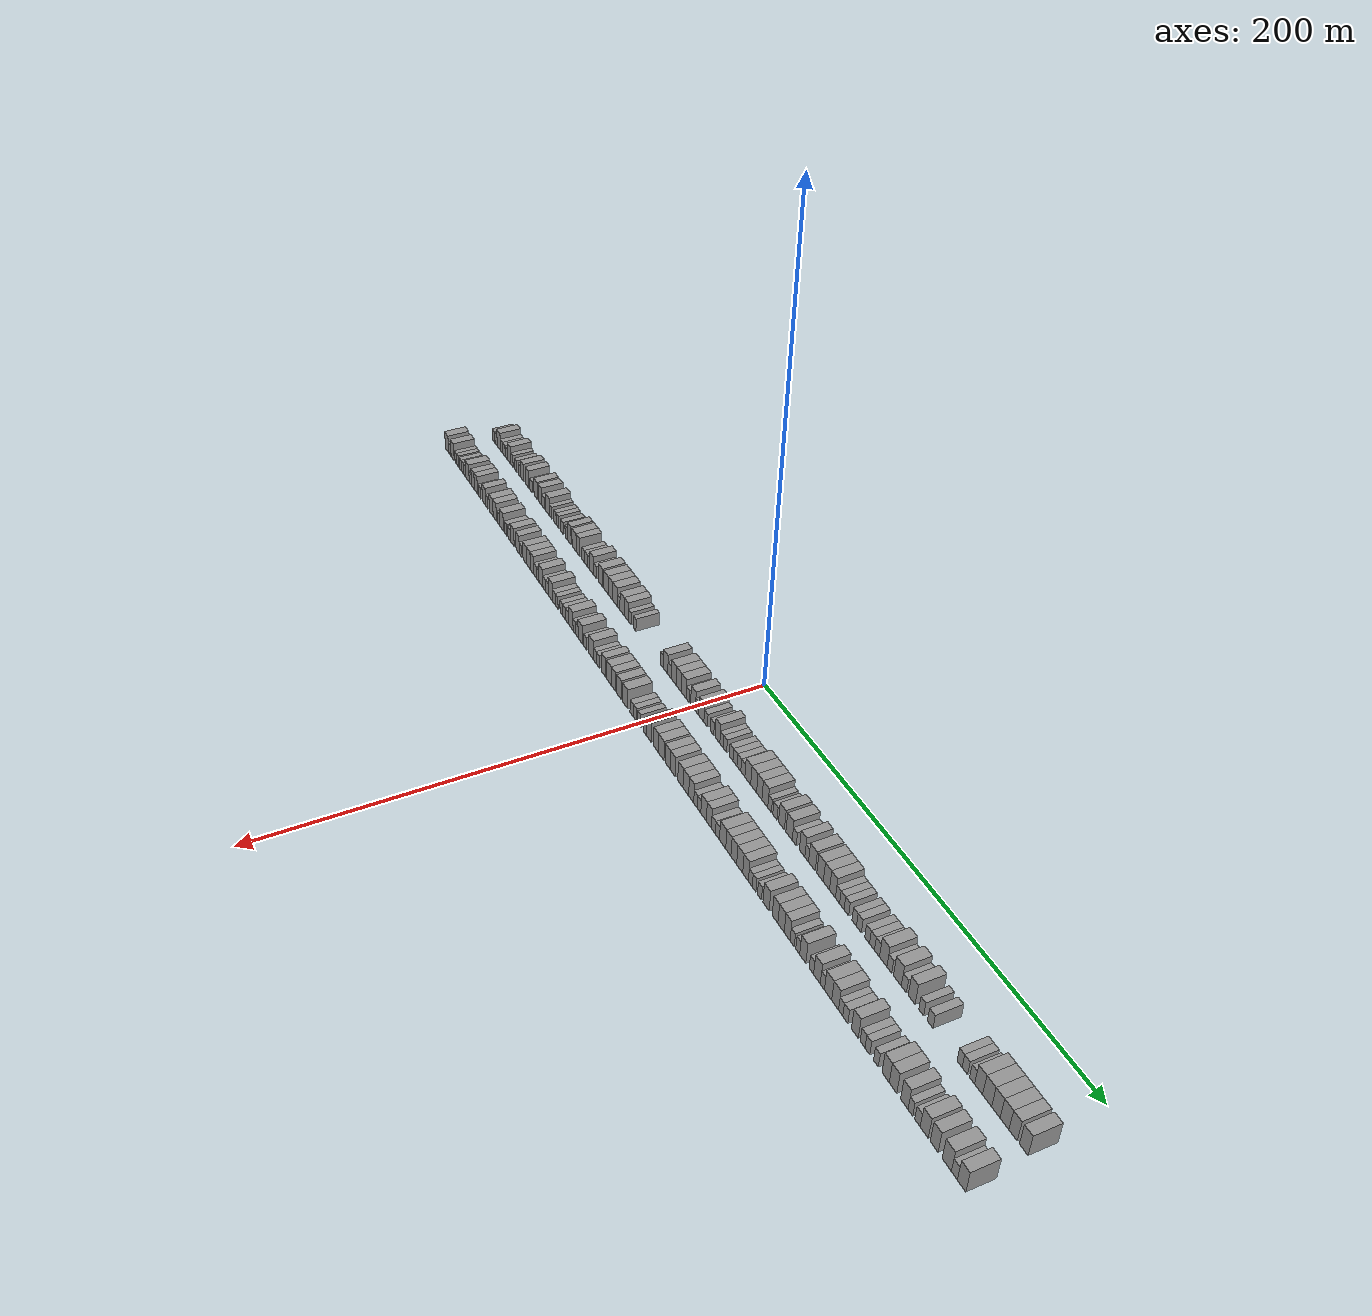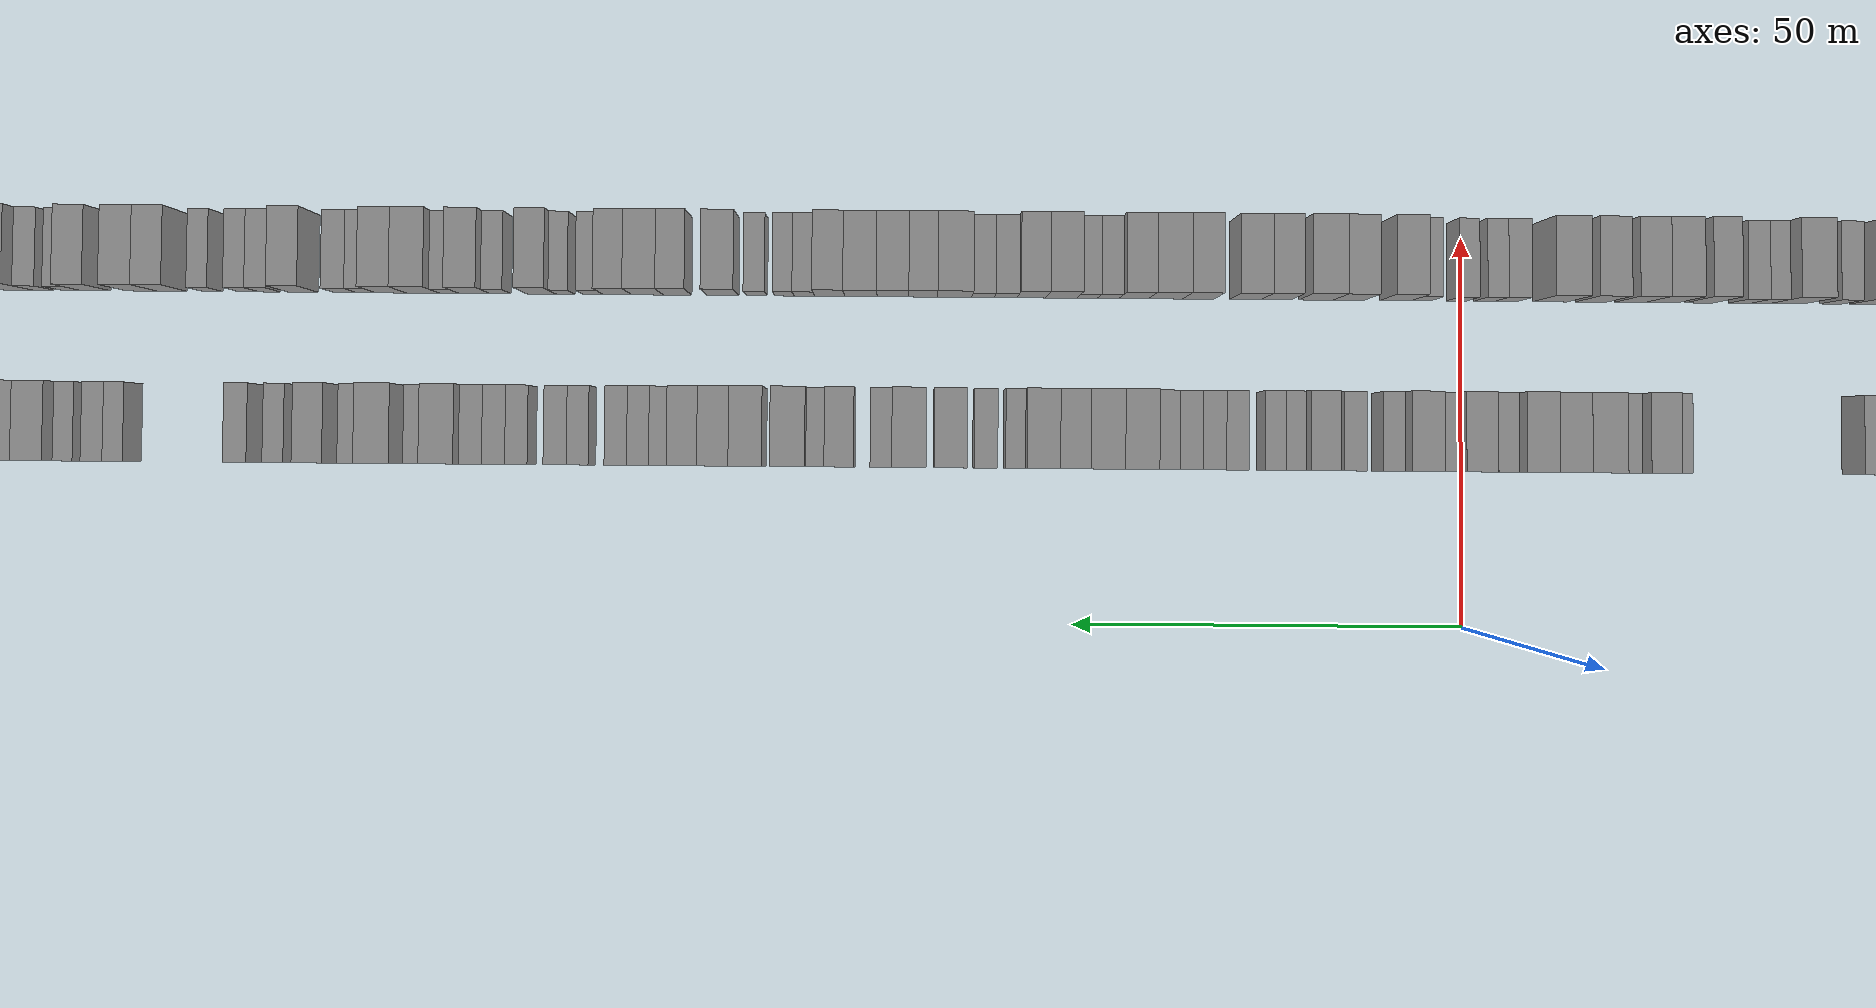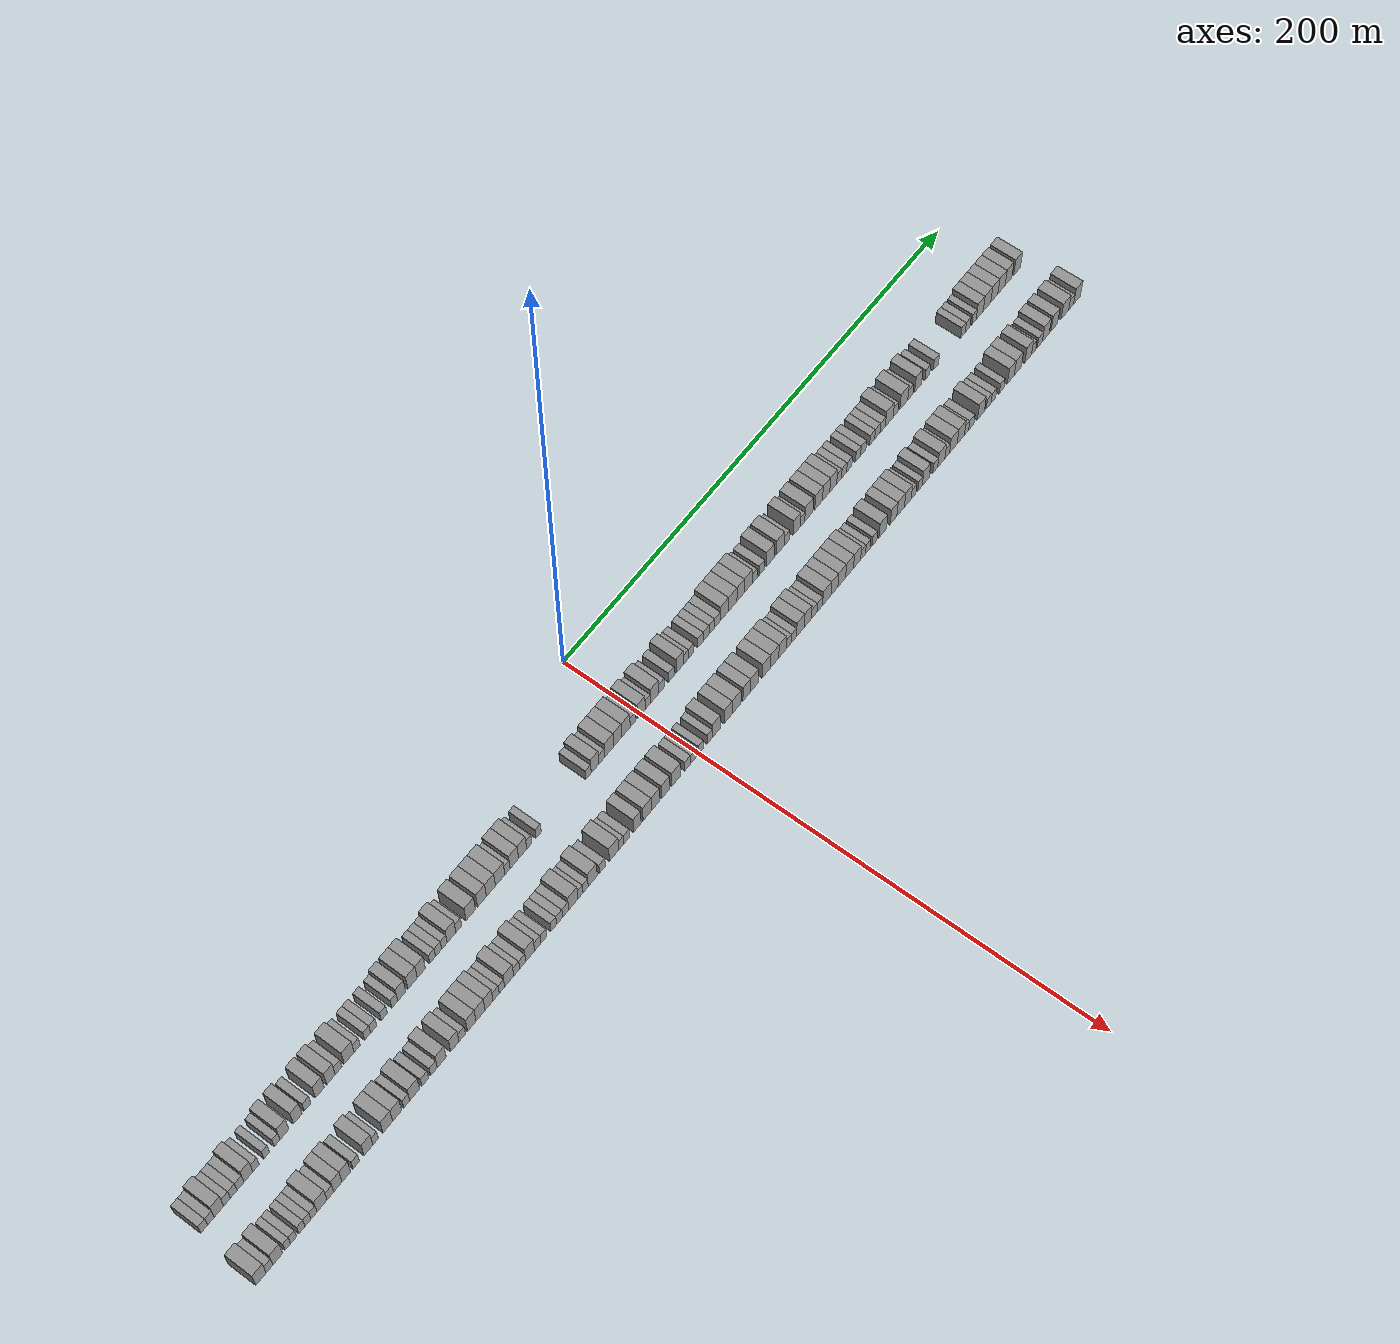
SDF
<sdf version="1.6">
 <world name="default">
  <scene>
   <sky><clouds><speed>12</speed></clouds></sky>
   <ambient>0.4 0.4 0.4 1</ambient>
   <background>0.7 0.7 0.7 1</background>
   <shadows>1</shadows>
  </scene>
  <gravity>0 0 -9.8066</gravity>
  <magnetic_field>6e-06 2.3e-05 -4.2e-05</magnetic_field>
  <physics default="0" name="default_physics" type="ode">
   <ode>
    <solver>
     <type>quick</type>
     <iters>10</iters>
     <sor>1.0</sor>
     <use_dynamic_moi_rescaling>0</use_dynamic_moi_rescaling>
    </solver>
    <constraints>
     <cfm>0</cfm>
     <erp>0.2</erp>
     <contact_max_correcting_vel>100</contact_max_correcting_vel>
     <contact_surface_layer>0.001</contact_surface_layer>
    </constraints>
   </ode>
   <max_step_size>0.004</max_step_size>
   <real_time_factor>1</real_time_factor>
   <real_time_update_rate>250</real_time_update_rate>
  </physics>
  <light name="sun" type="directional">
   <pose>0 0 10 0 0 0</pose>
   <diffuse>0.8 0.8 0.8 1</diffuse>
   <specular>0.2 0.2 0.2 1</specular>
   <attenuation>
    <range>1000</range>
    <constant>0.9</constant>
    <linear>0.01</linear>
    <quadratic>0.001</quadratic>
   </attenuation>
   <direction>-0.5 0.1 -0.9</direction>
  </light>
  <model name="building_1">
   <static>1</static>
   <pose>25.0000 -200.5337 0 0.000000 0.000000 0.000000</pose>
   <link name="link">
    <pose>0 0 3.00 0 0 0</pose>
    <collision name="collision"><geometry><box><size>10.0000 2.9326 6.0000</size></box></geometry></collision>
    <visual name="visual">
     <cast_shadows>0</cast_shadows>
     <geometry><box><size>10.0000 2.9326 6.0000</size></box></geometry>
     <material>
      <script>
       <uri>model://grey_wall/materials/scripts</uri>
       <uri>model://grey_wall/materials/textures</uri>
       <name>vrc/grey_wall</name>
      </script>
     </material>
    </visual>
   </link>
  </model>
  <model name="building_2">
   <static>1</static>
   <pose>25.0000 -197.6434 0 0.000000 0.000000 0.000000</pose>
   <link name="link">
    <pose>0 0 3.00 0 0 0</pose>
    <collision name="collision"><geometry><box><size>10.0000 2.8480 6.0000</size></box></geometry></collision>
    <visual name="visual">
     <cast_shadows>0</cast_shadows>
     <geometry><box><size>10.0000 2.8480 6.0000</size></box></geometry>
     <material>
      <script>
       <uri>model://grey_wall/materials/scripts</uri>
       <uri>model://grey_wall/materials/textures</uri>
       <name>vrc/grey_wall</name>
      </script>
     </material>
    </visual>
   </link>
  </model>
  <model name="building_3">
   <static>1</static>
   <pose>25.0000 -194.2087 0 0.000000 0.000000 0.000000</pose>
   <link name="link">
    <pose>0 0 4.50 0 0 0</pose>
    <collision name="collision"><geometry><box><size>10.0000 4.0214 9.0000</size></box></geometry></collision>
    <visual name="visual">
     <cast_shadows>0</cast_shadows>
     <geometry><box><size>10.0000 4.0214 9.0000</size></box></geometry>
     <material>
      <script>
       <uri>model://grey_wall/materials/scripts</uri>
       <uri>model://grey_wall/materials/textures</uri>
       <name>vrc/grey_wall</name>
      </script>
     </material>
    </visual>
   </link>
  </model>
  <model name="building_4">
   <static>1</static>
   <pose>25.0000 -190.7882 0 0.000000 0.000000 0.000000</pose>
   <link name="link">
    <pose>0 0 3.00 0 0 0</pose>
    <collision name="collision"><geometry><box><size>10.0000 2.8195 6.0000</size></box></geometry></collision>
    <visual name="visual">
     <cast_shadows>0</cast_shadows>
     <geometry><box><size>10.0000 2.8195 6.0000</size></box></geometry>
     <material>
      <script>
       <uri>model://grey_wall/materials/scripts</uri>
       <uri>model://grey_wall/materials/textures</uri>
       <name>vrc/grey_wall</name>
      </script>
     </material>
    </visual>
   </link>
  </model>
  <model name="building_5">
   <static>1</static>
   <pose>25.0000 -187.9269 0 0.000000 0.000000 0.000000</pose>
   <link name="link">
    <pose>0 0 3.00 0 0 0</pose>
    <collision name="collision"><geometry><box><size>10.0000 2.9031 6.0000</size></box></geometry></collision>
    <visual name="visual">
     <cast_shadows>0</cast_shadows>
     <geometry><box><size>10.0000 2.9031 6.0000</size></box></geometry>
     <material>
      <script>
       <uri>model://grey_wall/materials/scripts</uri>
       <uri>model://grey_wall/materials/textures</uri>
       <name>vrc/grey_wall</name>
      </script>
     </material>
    </visual>
   </link>
  </model>
  <model name="building_6">
   <static>1</static>
   <pose>25.0000 -185.0128 0 0.000000 0.000000 0.000000</pose>
   <link name="link">
    <pose>0 0 3.00 0 0 0</pose>
    <collision name="collision"><geometry><box><size>10.0000 2.9252 6.0000</size></box></geometry></collision>
    <visual name="visual">
     <cast_shadows>0</cast_shadows>
     <geometry><box><size>10.0000 2.9252 6.0000</size></box></geometry>
     <material>
      <script>
       <uri>model://grey_wall/materials/scripts</uri>
       <uri>model://grey_wall/materials/textures</uri>
       <name>vrc/grey_wall</name>
      </script>
     </material>
    </visual>
   </link>
  </model>
  <model name="building_7">
   <static>1</static>
   <pose>25.0000 -181.6386 0 0.000000 0.000000 0.000000</pose>
   <link name="link">
    <pose>0 0 4.50 0 0 0</pose>
    <collision name="collision"><geometry><box><size>10.0000 3.8232 9.0000</size></box></geometry></collision>
    <visual name="visual">
     <cast_shadows>0</cast_shadows>
     <geometry><box><size>10.0000 3.8232 9.0000</size></box></geometry>
     <material>
      <script>
       <uri>model://grey_wall/materials/scripts</uri>
       <uri>model://grey_wall/materials/textures</uri>
       <name>vrc/grey_wall</name>
      </script>
     </material>
    </visual>
   </link>
  </model>
  <model name="building_8">
   <static>1</static>
   <pose>25.0000 -178.3796 0 0.000000 0.000000 0.000000</pose>
   <link name="link">
    <pose>0 0 3.00 0 0 0</pose>
    <collision name="collision"><geometry><box><size>10.0000 2.6949 6.0000</size></box></geometry></collision>
    <visual name="visual">
     <cast_shadows>0</cast_shadows>
     <geometry><box><size>10.0000 2.6949 6.0000</size></box></geometry>
     <material>
      <script>
       <uri>model://grey_wall/materials/scripts</uri>
       <uri>model://grey_wall/materials/textures</uri>
       <name>vrc/grey_wall</name>
      </script>
     </material>
    </visual>
   </link>
  </model>
  <model name="building_9">
   <static>1</static>
   <pose>25.0000 -173.8010 0 0.000000 0.000000 0.000000</pose>
   <link name="link">
    <pose>0 0 3.00 0 0 0</pose>
    <collision name="collision"><geometry><box><size>10.0000 2.4623 6.0000</size></box></geometry></collision>
    <visual name="visual">
     <cast_shadows>0</cast_shadows>
     <geometry><box><size>10.0000 2.4623 6.0000</size></box></geometry>
     <material>
      <script>
       <uri>model://grey_wall/materials/scripts</uri>
       <uri>model://grey_wall/materials/textures</uri>
       <name>vrc/grey_wall</name>
      </script>
     </material>
    </visual>
   </link>
  </model>
  <model name="building_10">
   <static>1</static>
   <pose>25.0000 -169.3155 0 0.000000 0.000000 0.000000</pose>
   <link name="link">
    <pose>0 0 3.00 0 0 0</pose>
    <collision name="collision"><geometry><box><size>10.0000 2.5087 6.0000</size></box></geometry></collision>
    <visual name="visual">
     <cast_shadows>0</cast_shadows>
     <geometry><box><size>10.0000 2.5087 6.0000</size></box></geometry>
     <material>
      <script>
       <uri>model://grey_wall/materials/scripts</uri>
       <uri>model://grey_wall/materials/textures</uri>
       <name>vrc/grey_wall</name>
      </script>
     </material>
    </visual>
   </link>
  </model>
  <model name="building_11">
   <static>1</static>
   <pose>25.0000 -166.1479 0 0.000000 0.000000 0.000000</pose>
   <link name="link">
    <pose>0 0 4.50 0 0 0</pose>
    <collision name="collision"><geometry><box><size>10.0000 3.8265 9.0000</size></box></geometry></collision>
    <visual name="visual">
     <cast_shadows>0</cast_shadows>
     <geometry><box><size>10.0000 3.8265 9.0000</size></box></geometry>
     <material>
      <script>
       <uri>model://grey_wall/materials/scripts</uri>
       <uri>model://grey_wall/materials/textures</uri>
       <name>vrc/grey_wall</name>
      </script>
     </material>
    </visual>
   </link>
  </model>
  <model name="building_12">
   <static>1</static>
   <pose>25.0000 -160.3497 0 0.000000 0.000000 0.000000</pose>
   <link name="link">
    <pose>0 0 4.50 0 0 0</pose>
    <collision name="collision"><geometry><box><size>10.0000 3.7699 9.0000</size></box></geometry></collision>
    <visual name="visual">
     <cast_shadows>0</cast_shadows>
     <geometry><box><size>10.0000 3.7699 9.0000</size></box></geometry>
     <material>
      <script>
       <uri>model://grey_wall/materials/scripts</uri>
       <uri>model://grey_wall/materials/textures</uri>
       <name>vrc/grey_wall</name>
      </script>
     </material>
    </visual>
   </link>
  </model>
  <model name="building_13">
   <static>1</static>
   <pose>25.0000 -156.0359 0 0.000000 0.000000 0.000000</pose>
   <link name="link">
    <pose>0 0 3.00 0 0 0</pose>
    <collision name="collision"><geometry><box><size>10.0000 2.8578 6.0000</size></box></geometry></collision>
    <visual name="visual">
     <cast_shadows>0</cast_shadows>
     <geometry><box><size>10.0000 2.8578 6.0000</size></box></geometry>
     <material>
      <script>
       <uri>model://grey_wall/materials/scripts</uri>
       <uri>model://grey_wall/materials/textures</uri>
       <name>vrc/grey_wall</name>
      </script>
     </material>
    </visual>
   </link>
  </model>
  <model name="building_14">
   <static>1</static>
   <pose>25.0000 -150.6478 0 0.000000 0.000000 0.000000</pose>
   <link name="link">
    <pose>0 0 4.50 0 0 0</pose>
    <collision name="collision"><geometry><box><size>10.0000 3.9184 9.0000</size></box></geometry></collision>
    <visual name="visual">
     <cast_shadows>0</cast_shadows>
     <geometry><box><size>10.0000 3.9184 9.0000</size></box></geometry>
     <material>
      <script>
       <uri>model://grey_wall/materials/scripts</uri>
       <uri>model://grey_wall/materials/textures</uri>
       <name>vrc/grey_wall</name>
      </script>
     </material>
    </visual>
   </link>
  </model>
  <model name="building_15">
   <static>1</static>
   <pose>25.0000 -145.7635 0 0.000000 0.000000 0.000000</pose>
   <link name="link">
    <pose>0 0 4.50 0 0 0</pose>
    <collision name="collision"><geometry><box><size>10.0000 3.8500 9.0000</size></box></geometry></collision>
    <visual name="visual">
     <cast_shadows>0</cast_shadows>
     <geometry><box><size>10.0000 3.8500 9.0000</size></box></geometry>
     <material>
      <script>
       <uri>model://grey_wall/materials/scripts</uri>
       <uri>model://grey_wall/materials/textures</uri>
       <name>vrc/grey_wall</name>
      </script>
     </material>
    </visual>
   </link>
  </model>
  <model name="building_16">
   <static>1</static>
   <pose>25.0000 -142.3542 0 0.000000 0.000000 0.000000</pose>
   <link name="link">
    <pose>0 0 3.00 0 0 0</pose>
    <collision name="collision"><geometry><box><size>10.0000 2.9686 6.0000</size></box></geometry></collision>
    <visual name="visual">
     <cast_shadows>0</cast_shadows>
     <geometry><box><size>10.0000 2.9686 6.0000</size></box></geometry>
     <material>
      <script>
       <uri>model://grey_wall/materials/scripts</uri>
       <uri>model://grey_wall/materials/textures</uri>
       <name>vrc/grey_wall</name>
      </script>
     </material>
    </visual>
   </link>
  </model>
  <model name="building_17">
   <static>1</static>
   <pose>25.0000 -137.6517 0 0.000000 0.000000 0.000000</pose>
   <link name="link">
    <pose>0 0 4.50 0 0 0</pose>
    <collision name="collision"><geometry><box><size>10.0000 4.4365 9.0000</size></box></geometry></collision>
    <visual name="visual">
     <cast_shadows>0</cast_shadows>
     <geometry><box><size>10.0000 4.4365 9.0000</size></box></geometry>
     <material>
      <script>
       <uri>model://grey_wall/materials/scripts</uri>
       <uri>model://grey_wall/materials/textures</uri>
       <name>vrc/grey_wall</name>
      </script>
     </material>
    </visual>
   </link>
  </model>
  <model name="building_18">
   <static>1</static>
   <pose>25.0000 -134.0918 0 0.000000 0.000000 0.000000</pose>
   <link name="link">
    <pose>0 0 3.00 0 0 0</pose>
    <collision name="collision"><geometry><box><size>10.0000 2.6832 6.0000</size></box></geometry></collision>
    <visual name="visual">
     <cast_shadows>0</cast_shadows>
     <geometry><box><size>10.0000 2.6832 6.0000</size></box></geometry>
     <material>
      <script>
       <uri>model://grey_wall/materials/scripts</uri>
       <uri>model://grey_wall/materials/textures</uri>
       <name>vrc/grey_wall</name>
      </script>
     </material>
    </visual>
   </link>
  </model>
  <model name="building_19">
   <static>1</static>
   <pose>25.0000 -129.4211 0 0.000000 0.000000 0.000000</pose>
   <link name="link">
    <pose>0 0 3.00 0 0 0</pose>
    <collision name="collision"><geometry><box><size>10.0000 2.6581 6.0000</size></box></geometry></collision>
    <visual name="visual">
     <cast_shadows>0</cast_shadows>
     <geometry><box><size>10.0000 2.6581 6.0000</size></box></geometry>
     <material>
      <script>
       <uri>model://grey_wall/materials/scripts</uri>
       <uri>model://grey_wall/materials/textures</uri>
       <name>vrc/grey_wall</name>
      </script>
     </material>
    </visual>
   </link>
  </model>
  <model name="building_20">
   <static>1</static>
   <pose>25.0000 -126.7219 0 0.000000 0.000000 0.000000</pose>
   <link name="link">
    <pose>0 0 3.00 0 0 0</pose>
    <collision name="collision"><geometry><box><size>10.0000 2.7403 6.0000</size></box></geometry></collision>
    <visual name="visual">
     <cast_shadows>0</cast_shadows>
     <geometry><box><size>10.0000 2.7403 6.0000</size></box></geometry>
     <material>
      <script>
       <uri>model://grey_wall/materials/scripts</uri>
       <uri>model://grey_wall/materials/textures</uri>
       <name>vrc/grey_wall</name>
      </script>
     </material>
    </visual>
   </link>
  </model>
  <model name="building_21">
   <static>1</static>
   <pose>25.0000 -121.9303 0 0.000000 0.000000 0.000000</pose>
   <link name="link">
    <pose>0 0 3.00 0 0 0</pose>
    <collision name="collision"><geometry><box><size>10.0000 2.8429 6.0000</size></box></geometry></collision>
    <visual name="visual">
     <cast_shadows>0</cast_shadows>
     <geometry><box><size>10.0000 2.8429 6.0000</size></box></geometry>
     <material>
      <script>
       <uri>model://grey_wall/materials/scripts</uri>
       <uri>model://grey_wall/materials/textures</uri>
       <name>vrc/grey_wall</name>
      </script>
     </material>
    </visual>
   </link>
  </model>
  <model name="building_22">
   <static>1</static>
   <pose>25.0000 -117.1746 0 0.000000 0.000000 0.000000</pose>
   <link name="link">
    <pose>0 0 3.00 0 0 0</pose>
    <collision name="collision"><geometry><box><size>10.0000 2.6685 6.0000</size></box></geometry></collision>
    <visual name="visual">
     <cast_shadows>0</cast_shadows>
     <geometry><box><size>10.0000 2.6685 6.0000</size></box></geometry>
     <material>
      <script>
       <uri>model://grey_wall/materials/scripts</uri>
       <uri>model://grey_wall/materials/textures</uri>
       <name>vrc/grey_wall</name>
      </script>
     </material>
    </visual>
   </link>
  </model>
  <model name="building_23">
   <static>1</static>
   <pose>25.0000 -114.0231 0 0.000000 0.000000 0.000000</pose>
   <link name="link">
    <pose>0 0 4.50 0 0 0</pose>
    <collision name="collision"><geometry><box><size>10.0000 3.6344 9.0000</size></box></geometry></collision>
    <visual name="visual">
     <cast_shadows>0</cast_shadows>
     <geometry><box><size>10.0000 3.6344 9.0000</size></box></geometry>
     <material>
      <script>
       <uri>model://grey_wall/materials/scripts</uri>
       <uri>model://grey_wall/materials/textures</uri>
       <name>vrc/grey_wall</name>
      </script>
     </material>
    </visual>
   </link>
  </model>
  <model name="building_24">
   <static>1</static>
   <pose>25.0000 -109.0692 0 0.000000 0.000000 0.000000</pose>
   <link name="link">
    <pose>0 0 4.50 0 0 0</pose>
    <collision name="collision"><geometry><box><size>10.0000 4.2735 9.0000</size></box></geometry></collision>
    <visual name="visual">
     <cast_shadows>0</cast_shadows>
     <geometry><box><size>10.0000 4.2735 9.0000</size></box></geometry>
     <material>
      <script>
       <uri>model://grey_wall/materials/scripts</uri>
       <uri>model://grey_wall/materials/textures</uri>
       <name>vrc/grey_wall</name>
      </script>
     </material>
    </visual>
   </link>
  </model>
  <model name="building_25">
   <static>1</static>
   <pose>25.0000 -105.0818 0 0.000000 0.000000 0.000000</pose>
   <link name="link">
    <pose>0 0 4.50 0 0 0</pose>
    <collision name="collision"><geometry><box><size>10.0000 3.7013 9.0000</size></box></geometry></collision>
    <visual name="visual">
     <cast_shadows>0</cast_shadows>
     <geometry><box><size>10.0000 3.7013 9.0000</size></box></geometry>
     <material>
      <script>
       <uri>model://grey_wall/materials/scripts</uri>
       <uri>model://grey_wall/materials/textures</uri>
       <name>vrc/grey_wall</name>
      </script>
     </material>
    </visual>
   </link>
  </model>
  <model name="building_26">
   <static>1</static>
   <pose>25.0000 -99.9082 0 0.000000 0.000000 0.000000</pose>
   <link name="link">
    <pose>0 0 3.00 0 0 0</pose>
    <collision name="collision"><geometry><box><size>10.0000 2.6459 6.0000</size></box></geometry></collision>
    <visual name="visual">
     <cast_shadows>0</cast_shadows>
     <geometry><box><size>10.0000 2.6459 6.0000</size></box></geometry>
     <material>
      <script>
       <uri>model://grey_wall/materials/scripts</uri>
       <uri>model://grey_wall/materials/textures</uri>
       <name>vrc/grey_wall</name>
      </script>
     </material>
    </visual>
   </link>
  </model>
  <model name="building_27">
   <static>1</static>
   <pose>25.0000 -97.1660 0 0.000000 0.000000 0.000000</pose>
   <link name="link">
    <pose>0 0 3.00 0 0 0</pose>
    <collision name="collision"><geometry><box><size>10.0000 2.8386 6.0000</size></box></geometry></collision>
    <visual name="visual">
     <cast_shadows>0</cast_shadows>
     <geometry><box><size>10.0000 2.8386 6.0000</size></box></geometry>
     <material>
      <script>
       <uri>model://grey_wall/materials/scripts</uri>
       <uri>model://grey_wall/materials/textures</uri>
       <name>vrc/grey_wall</name>
      </script>
     </material>
    </visual>
   </link>
  </model>
  <model name="building_28">
   <static>1</static>
   <pose>25.0000 -94.4889 0 0.000000 0.000000 0.000000</pose>
   <link name="link">
    <pose>0 0 3.00 0 0 0</pose>
    <collision name="collision"><geometry><box><size>10.0000 2.5156 6.0000</size></box></geometry></collision>
    <visual name="visual">
     <cast_shadows>0</cast_shadows>
     <geometry><box><size>10.0000 2.5156 6.0000</size></box></geometry>
     <material>
      <script>
       <uri>model://grey_wall/materials/scripts</uri>
       <uri>model://grey_wall/materials/textures</uri>
       <name>vrc/grey_wall</name>
      </script>
     </material>
    </visual>
   </link>
  </model>
  <model name="building_29">
   <static>1</static>
   <pose>25.0000 -91.2158 0 0.000000 0.000000 0.000000</pose>
   <link name="link">
    <pose>0 0 4.50 0 0 0</pose>
    <collision name="collision"><geometry><box><size>10.0000 4.0306 9.0000</size></box></geometry></collision>
    <visual name="visual">
     <cast_shadows>0</cast_shadows>
     <geometry><box><size>10.0000 4.0306 9.0000</size></box></geometry>
     <material>
      <script>
       <uri>model://grey_wall/materials/scripts</uri>
       <uri>model://grey_wall/materials/textures</uri>
       <name>vrc/grey_wall</name>
      </script>
     </material>
    </visual>
   </link>
  </model>
  <model name="building_30">
   <static>1</static>
   <pose>25.0000 -87.8514 0 0.000000 0.000000 0.000000</pose>
   <link name="link">
    <pose>0 0 3.00 0 0 0</pose>
    <collision name="collision"><geometry><box><size>10.0000 2.6983 6.0000</size></box></geometry></collision>
    <visual name="visual">
     <cast_shadows>0</cast_shadows>
     <geometry><box><size>10.0000 2.6983 6.0000</size></box></geometry>
     <material>
      <script>
       <uri>model://grey_wall/materials/scripts</uri>
       <uri>model://grey_wall/materials/textures</uri>
       <name>vrc/grey_wall</name>
      </script>
     </material>
    </visual>
   </link>
  </model>
  <model name="building_31">
   <static>1</static>
   <pose>25.0000 -82.3057 0 0.000000 0.000000 0.000000</pose>
   <link name="link">
    <pose>0 0 4.50 0 0 0</pose>
    <collision name="collision"><geometry><box><size>10.0000 4.3931 9.0000</size></box></geometry></collision>
    <visual name="visual">
     <cast_shadows>0</cast_shadows>
     <geometry><box><size>10.0000 4.3931 9.0000</size></box></geometry>
     <material>
      <script>
       <uri>model://grey_wall/materials/scripts</uri>
       <uri>model://grey_wall/materials/textures</uri>
       <name>vrc/grey_wall</name>
      </script>
     </material>
    </visual>
   </link>
  </model>
  <model name="building_32">
   <static>1</static>
   <pose>25.0000 -77.0357 0 0.000000 0.000000 0.000000</pose>
   <link name="link">
    <pose>0 0 4.50 0 0 0</pose>
    <collision name="collision"><geometry><box><size>10.0000 4.1468 9.0000</size></box></geometry></collision>
    <visual name="visual">
     <cast_shadows>0</cast_shadows>
     <geometry><box><size>10.0000 4.1468 9.0000</size></box></geometry>
     <material>
      <script>
       <uri>model://grey_wall/materials/scripts</uri>
       <uri>model://grey_wall/materials/textures</uri>
       <name>vrc/grey_wall</name>
      </script>
     </material>
    </visual>
   </link>
  </model>
  <model name="building_33">
   <static>1</static>
   <pose>25.0000 -72.8409 0 0.000000 0.000000 0.000000</pose>
   <link name="link">
    <pose>0 0 4.50 0 0 0</pose>
    <collision name="collision"><geometry><box><size>10.0000 4.2428 9.0000</size></box></geometry></collision>
    <visual name="visual">
     <cast_shadows>0</cast_shadows>
     <geometry><box><size>10.0000 4.2428 9.0000</size></box></geometry>
     <material>
      <script>
       <uri>model://grey_wall/materials/scripts</uri>
       <uri>model://grey_wall/materials/textures</uri>
       <name>vrc/grey_wall</name>
      </script>
     </material>
    </visual>
   </link>
  </model>
  <model name="building_34">
   <static>1</static>
   <pose>25.0000 -68.4994 0 0.000000 0.000000 0.000000</pose>
   <link name="link">
    <pose>0 0 4.50 0 0 0</pose>
    <collision name="collision"><geometry><box><size>10.0000 4.4401 9.0000</size></box></geometry></collision>
    <visual name="visual">
     <cast_shadows>0</cast_shadows>
     <geometry><box><size>10.0000 4.4401 9.0000</size></box></geometry>
     <material>
      <script>
       <uri>model://grey_wall/materials/scripts</uri>
       <uri>model://grey_wall/materials/textures</uri>
       <name>vrc/grey_wall</name>
      </script>
     </material>
    </visual>
   </link>
  </model>
  <model name="building_35">
   <static>1</static>
   <pose>25.0000 -65.0476 0 0.000000 0.000000 0.000000</pose>
   <link name="link">
    <pose>0 0 3.00 0 0 0</pose>
    <collision name="collision"><geometry><box><size>10.0000 2.4635 6.0000</size></box></geometry></collision>
    <visual name="visual">
     <cast_shadows>0</cast_shadows>
     <geometry><box><size>10.0000 2.4635 6.0000</size></box></geometry>
     <material>
      <script>
       <uri>model://grey_wall/materials/scripts</uri>
       <uri>model://grey_wall/materials/textures</uri>
       <name>vrc/grey_wall</name>
      </script>
     </material>
    </visual>
   </link>
  </model>
  <model name="building_36">
   <static>1</static>
   <pose>25.0000 -61.7955 0 0.000000 0.000000 0.000000</pose>
   <link name="link">
    <pose>0 0 4.50 0 0 0</pose>
    <collision name="collision"><geometry><box><size>10.0000 4.0407 9.0000</size></box></geometry></collision>
    <visual name="visual">
     <cast_shadows>0</cast_shadows>
     <geometry><box><size>10.0000 4.0407 9.0000</size></box></geometry>
     <material>
      <script>
       <uri>model://grey_wall/materials/scripts</uri>
       <uri>model://grey_wall/materials/textures</uri>
       <name>vrc/grey_wall</name>
      </script>
     </material>
    </visual>
   </link>
  </model>
  <model name="building_37">
   <static>1</static>
   <pose>25.0000 -57.8602 0 0.000000 0.000000 0.000000</pose>
   <link name="link">
    <pose>0 0 4.50 0 0 0</pose>
    <collision name="collision"><geometry><box><size>10.0000 3.8299 9.0000</size></box></geometry></collision>
    <visual name="visual">
     <cast_shadows>0</cast_shadows>
     <geometry><box><size>10.0000 3.8299 9.0000</size></box></geometry>
     <material>
      <script>
       <uri>model://grey_wall/materials/scripts</uri>
       <uri>model://grey_wall/materials/textures</uri>
       <name>vrc/grey_wall</name>
      </script>
     </material>
    </visual>
   </link>
  </model>
  <model name="building_38">
   <static>1</static>
   <pose>25.0000 -54.7320 0 0.000000 0.000000 0.000000</pose>
   <link name="link">
    <pose>0 0 3.00 0 0 0</pose>
    <collision name="collision"><geometry><box><size>10.0000 2.4264 6.0000</size></box></geometry></collision>
    <visual name="visual">
     <cast_shadows>0</cast_shadows>
     <geometry><box><size>10.0000 2.4264 6.0000</size></box></geometry>
     <material>
      <script>
       <uri>model://grey_wall/materials/scripts</uri>
       <uri>model://grey_wall/materials/textures</uri>
       <name>vrc/grey_wall</name>
      </script>
     </material>
    </visual>
   </link>
  </model>
  <model name="building_39">
   <static>1</static>
   <pose>25.0000 -50.2527 0 0.000000 0.000000 0.000000</pose>
   <link name="link">
    <pose>0 0 3.00 0 0 0</pose>
    <collision name="collision"><geometry><box><size>10.0000 2.5323 6.0000</size></box></geometry></collision>
    <visual name="visual">
     <cast_shadows>0</cast_shadows>
     <geometry><box><size>10.0000 2.5323 6.0000</size></box></geometry>
     <material>
      <script>
       <uri>model://grey_wall/materials/scripts</uri>
       <uri>model://grey_wall/materials/textures</uri>
       <name>vrc/grey_wall</name>
      </script>
     </material>
    </visual>
   </link>
  </model>
  <model name="building_40">
   <static>1</static>
   <pose>25.0000 -26.1043 0 0.000000 0.000000 0.000000</pose>
   <link name="link">
    <pose>0 0 3.00 0 0 0</pose>
    <collision name="collision"><geometry><box><size>10.0000 2.5882 6.0000</size></box></geometry></collision>
    <visual name="visual">
     <cast_shadows>0</cast_shadows>
     <geometry><box><size>10.0000 2.5882 6.0000</size></box></geometry>
     <material>
      <script>
       <uri>model://grey_wall/materials/scripts</uri>
       <uri>model://grey_wall/materials/textures</uri>
       <name>vrc/grey_wall</name>
      </script>
     </material>
    </visual>
   </link>
  </model>
  <model name="building_41">
   <static>1</static>
   <pose>25.0000 -22.9158 0 0.000000 0.000000 0.000000</pose>
   <link name="link">
    <pose>0 0 4.50 0 0 0</pose>
    <collision name="collision"><geometry><box><size>10.0000 3.7887 9.0000</size></box></geometry></collision>
    <visual name="visual">
     <cast_shadows>0</cast_shadows>
     <geometry><box><size>10.0000 3.7887 9.0000</size></box></geometry>
     <material>
      <script>
       <uri>model://grey_wall/materials/scripts</uri>
       <uri>model://grey_wall/materials/textures</uri>
       <name>vrc/grey_wall</name>
      </script>
     </material>
    </visual>
   </link>
  </model>
  <model name="building_42">
   <static>1</static>
   <pose>25.0000 -19.5918 0 0.000000 0.000000 0.000000</pose>
   <link name="link">
    <pose>0 0 3.00 0 0 0</pose>
    <collision name="collision"><geometry><box><size>10.0000 2.8595 6.0000</size></box></geometry></collision>
    <visual name="visual">
     <cast_shadows>0</cast_shadows>
     <geometry><box><size>10.0000 2.8595 6.0000</size></box></geometry>
     <material>
      <script>
       <uri>model://grey_wall/materials/scripts</uri>
       <uri>model://grey_wall/materials/textures</uri>
       <name>vrc/grey_wall</name>
      </script>
     </material>
    </visual>
   </link>
  </model>
  <model name="building_43">
   <static>1</static>
   <pose>25.0000 -15.9503 0 0.000000 0.000000 0.000000</pose>
   <link name="link">
    <pose>0 0 4.50 0 0 0</pose>
    <collision name="collision"><geometry><box><size>10.0000 4.4235 9.0000</size></box></geometry></collision>
    <visual name="visual">
     <cast_shadows>0</cast_shadows>
     <geometry><box><size>10.0000 4.4235 9.0000</size></box></geometry>
     <material>
      <script>
       <uri>model://grey_wall/materials/scripts</uri>
       <uri>model://grey_wall/materials/textures</uri>
       <name>vrc/grey_wall</name>
      </script>
     </material>
    </visual>
   </link>
  </model>
  <model name="building_44">
   <static>1</static>
   <pose>25.0000 -11.7266 0 0.000000 0.000000 0.000000</pose>
   <link name="link">
    <pose>0 0 4.50 0 0 0</pose>
    <collision name="collision"><geometry><box><size>10.0000 4.0238 9.0000</size></box></geometry></collision>
    <visual name="visual">
     <cast_shadows>0</cast_shadows>
     <geometry><box><size>10.0000 4.0238 9.0000</size></box></geometry>
     <material>
      <script>
       <uri>model://grey_wall/materials/scripts</uri>
       <uri>model://grey_wall/materials/textures</uri>
       <name>vrc/grey_wall</name>
      </script>
     </material>
    </visual>
   </link>
  </model>
  <model name="building_45">
   <static>1</static>
   <pose>25.0000 -7.6589 0 0.000000 0.000000 0.000000</pose>
   <link name="link">
    <pose>0 0 4.50 0 0 0</pose>
    <collision name="collision"><geometry><box><size>10.0000 4.1117 9.0000</size></box></geometry></collision>
    <visual name="visual">
     <cast_shadows>0</cast_shadows>
     <geometry><box><size>10.0000 4.1117 9.0000</size></box></geometry>
     <material>
      <script>
       <uri>model://grey_wall/materials/scripts</uri>
       <uri>model://grey_wall/materials/textures</uri>
       <name>vrc/grey_wall</name>
      </script>
     </material>
    </visual>
   </link>
  </model>
  <model name="building_46">
   <static>1</static>
   <pose>25.0000 -4.2922 0 0.000000 0.000000 0.000000</pose>
   <link name="link">
    <pose>0 0 3.00 0 0 0</pose>
    <collision name="collision"><geometry><box><size>10.0000 2.6216 6.0000</size></box></geometry></collision>
    <visual name="visual">
     <cast_shadows>0</cast_shadows>
     <geometry><box><size>10.0000 2.6216 6.0000</size></box></geometry>
     <material>
      <script>
       <uri>model://grey_wall/materials/scripts</uri>
       <uri>model://grey_wall/materials/textures</uri>
       <name>vrc/grey_wall</name>
      </script>
     </material>
    </visual>
   </link>
  </model>
  <model name="building_47">
   <static>1</static>
   <pose>25.0000 -0.0352 0 0.000000 0.000000 0.000000</pose>
   <link name="link">
    <pose>0 0 4.50 0 0 0</pose>
    <collision name="collision"><geometry><box><size>10.0000 3.8925 9.0000</size></box></geometry></collision>
    <visual name="visual">
     <cast_shadows>0</cast_shadows>
     <geometry><box><size>10.0000 3.8925 9.0000</size></box></geometry>
     <material>
      <script>
       <uri>model://grey_wall/materials/scripts</uri>
       <uri>model://grey_wall/materials/textures</uri>
       <name>vrc/grey_wall</name>
      </script>
     </material>
    </visual>
   </link>
  </model>
  <model name="building_48">
   <static>1</static>
   <pose>25.0000 3.2444 0 0.000000 0.000000 0.000000</pose>
   <link name="link">
    <pose>0 0 3.00 0 0 0</pose>
    <collision name="collision"><geometry><box><size>10.0000 2.6667 6.0000</size></box></geometry></collision>
    <visual name="visual">
     <cast_shadows>0</cast_shadows>
     <geometry><box><size>10.0000 2.6667 6.0000</size></box></geometry>
     <material>
      <script>
       <uri>model://grey_wall/materials/scripts</uri>
       <uri>model://grey_wall/materials/textures</uri>
       <name>vrc/grey_wall</name>
      </script>
     </material>
    </visual>
   </link>
  </model>
  <model name="building_49">
   <static>1</static>
   <pose>25.0000 6.6460 0 0.000000 0.000000 0.000000</pose>
   <link name="link">
    <pose>0 0 4.50 0 0 0</pose>
    <collision name="collision"><geometry><box><size>10.0000 4.1365 9.0000</size></box></geometry></collision>
    <visual name="visual">
     <cast_shadows>0</cast_shadows>
     <geometry><box><size>10.0000 4.1365 9.0000</size></box></geometry>
     <material>
      <script>
       <uri>model://grey_wall/materials/scripts</uri>
       <uri>model://grey_wall/materials/textures</uri>
       <name>vrc/grey_wall</name>
      </script>
     </material>
    </visual>
   </link>
  </model>
  <model name="building_50">
   <static>1</static>
   <pose>25.0000 10.1322 0 0.000000 0.000000 0.000000</pose>
   <link name="link">
    <pose>0 0 3.00 0 0 0</pose>
    <collision name="collision"><geometry><box><size>10.0000 2.8359 6.0000</size></box></geometry></collision>
    <visual name="visual">
     <cast_shadows>0</cast_shadows>
     <geometry><box><size>10.0000 2.8359 6.0000</size></box></geometry>
     <material>
      <script>
       <uri>model://grey_wall/materials/scripts</uri>
       <uri>model://grey_wall/materials/textures</uri>
       <name>vrc/grey_wall</name>
      </script>
     </material>
    </visual>
   </link>
  </model>
  <model name="building_51">
   <static>1</static>
   <pose>25.0000 14.9965 0 0.000000 0.000000 0.000000</pose>
   <link name="link">
    <pose>0 0 3.00 0 0 0</pose>
    <collision name="collision"><geometry><box><size>10.0000 2.8928 6.0000</size></box></geometry></collision>
    <visual name="visual">
     <cast_shadows>0</cast_shadows>
     <geometry><box><size>10.0000 2.8928 6.0000</size></box></geometry>
     <material>
      <script>
       <uri>model://grey_wall/materials/scripts</uri>
       <uri>model://grey_wall/materials/textures</uri>
       <name>vrc/grey_wall</name>
      </script>
     </material>
    </visual>
   </link>
  </model>
  <model name="building_52">
   <static>1</static>
   <pose>25.0000 19.3135 0 0.000000 0.000000 0.000000</pose>
   <link name="link">
    <pose>0 0 4.50 0 0 0</pose>
    <collision name="collision"><geometry><box><size>10.0000 3.7412 9.0000</size></box></geometry></collision>
    <visual name="visual">
     <cast_shadows>0</cast_shadows>
     <geometry><box><size>10.0000 3.7412 9.0000</size></box></geometry>
     <material>
      <script>
       <uri>model://grey_wall/materials/scripts</uri>
       <uri>model://grey_wall/materials/textures</uri>
       <name>vrc/grey_wall</name>
      </script>
     </material>
    </visual>
   </link>
  </model>
  <model name="building_53">
   <static>1</static>
   <pose>25.0000 22.4335 0 0.000000 0.000000 0.000000</pose>
   <link name="link">
    <pose>0 0 3.00 0 0 0</pose>
    <collision name="collision"><geometry><box><size>10.0000 2.4987 6.0000</size></box></geometry></collision>
    <visual name="visual">
     <cast_shadows>0</cast_shadows>
     <geometry><box><size>10.0000 2.4987 6.0000</size></box></geometry>
     <material>
      <script>
       <uri>model://grey_wall/materials/scripts</uri>
       <uri>model://grey_wall/materials/textures</uri>
       <name>vrc/grey_wall</name>
      </script>
     </material>
    </visual>
   </link>
  </model>
  <model name="building_54">
   <static>1</static>
   <pose>25.0000 25.0154 0 0.000000 0.000000 0.000000</pose>
   <link name="link">
    <pose>0 0 3.00 0 0 0</pose>
    <collision name="collision"><geometry><box><size>10.0000 2.6651 6.0000</size></box></geometry></collision>
    <visual name="visual">
     <cast_shadows>0</cast_shadows>
     <geometry><box><size>10.0000 2.6651 6.0000</size></box></geometry>
     <material>
      <script>
       <uri>model://grey_wall/materials/scripts</uri>
       <uri>model://grey_wall/materials/textures</uri>
       <name>vrc/grey_wall</name>
      </script>
     </material>
    </visual>
   </link>
  </model>
  <model name="building_55">
   <static>1</static>
   <pose>25.0000 29.7597 0 0.000000 0.000000 0.000000</pose>
   <link name="link">
    <pose>0 0 3.00 0 0 0</pose>
    <collision name="collision"><geometry><box><size>10.0000 2.8235 6.0000</size></box></geometry></collision>
    <visual name="visual">
     <cast_shadows>0</cast_shadows>
     <geometry><box><size>10.0000 2.8235 6.0000</size></box></geometry>
     <material>
      <script>
       <uri>model://grey_wall/materials/scripts</uri>
       <uri>model://grey_wall/materials/textures</uri>
       <name>vrc/grey_wall</name>
      </script>
     </material>
    </visual>
   </link>
  </model>
  <model name="building_56">
   <static>1</static>
   <pose>25.0000 32.6455 0 0.000000 0.000000 0.000000</pose>
   <link name="link">
    <pose>0 0 3.00 0 0 0</pose>
    <collision name="collision"><geometry><box><size>10.0000 2.9481 6.0000</size></box></geometry></collision>
    <visual name="visual">
     <cast_shadows>0</cast_shadows>
     <geometry><box><size>10.0000 2.9481 6.0000</size></box></geometry>
     <material>
      <script>
       <uri>model://grey_wall/materials/scripts</uri>
       <uri>model://grey_wall/materials/textures</uri>
       <name>vrc/grey_wall</name>
      </script>
     </material>
    </visual>
   </link>
  </model>
  <model name="building_57">
   <static>1</static>
   <pose>25.0000 35.5581 0 0.000000 0.000000 0.000000</pose>
   <link name="link">
    <pose>0 0 3.00 0 0 0</pose>
    <collision name="collision"><geometry><box><size>10.0000 2.8771 6.0000</size></box></geometry></collision>
    <visual name="visual">
     <cast_shadows>0</cast_shadows>
     <geometry><box><size>10.0000 2.8771 6.0000</size></box></geometry>
     <material>
      <script>
       <uri>model://grey_wall/materials/scripts</uri>
       <uri>model://grey_wall/materials/textures</uri>
       <name>vrc/grey_wall</name>
      </script>
     </material>
    </visual>
   </link>
  </model>
  <model name="building_58">
   <static>1</static>
   <pose>25.0000 38.4874 0 0.000000 0.000000 0.000000</pose>
   <link name="link">
    <pose>0 0 3.00 0 0 0</pose>
    <collision name="collision"><geometry><box><size>10.0000 2.9816 6.0000</size></box></geometry></collision>
    <visual name="visual">
     <cast_shadows>0</cast_shadows>
     <geometry><box><size>10.0000 2.9816 6.0000</size></box></geometry>
     <material>
      <script>
       <uri>model://grey_wall/materials/scripts</uri>
       <uri>model://grey_wall/materials/textures</uri>
       <name>vrc/grey_wall</name>
      </script>
     </material>
    </visual>
   </link>
  </model>
  <model name="building_59">
   <static>1</static>
   <pose>25.0000 42.0913 0 0.000000 0.000000 0.000000</pose>
   <link name="link">
    <pose>0 0 4.50 0 0 0</pose>
    <collision name="collision"><geometry><box><size>10.0000 4.2262 9.0000</size></box></geometry></collision>
    <visual name="visual">
     <cast_shadows>0</cast_shadows>
     <geometry><box><size>10.0000 4.2262 9.0000</size></box></geometry>
     <material>
      <script>
       <uri>model://grey_wall/materials/scripts</uri>
       <uri>model://grey_wall/materials/textures</uri>
       <name>vrc/grey_wall</name>
      </script>
     </material>
    </visual>
   </link>
  </model>
  <model name="building_60">
   <static>1</static>
   <pose>25.0000 46.3436 0 0.000000 0.000000 0.000000</pose>
   <link name="link">
    <pose>0 0 4.50 0 0 0</pose>
    <collision name="collision"><geometry><box><size>10.0000 4.2783 9.0000</size></box></geometry></collision>
    <visual name="visual">
     <cast_shadows>0</cast_shadows>
     <geometry><box><size>10.0000 4.2783 9.0000</size></box></geometry>
     <material>
      <script>
       <uri>model://grey_wall/materials/scripts</uri>
       <uri>model://grey_wall/materials/textures</uri>
       <name>vrc/grey_wall</name>
      </script>
     </material>
    </visual>
   </link>
  </model>
  <model name="building_61">
   <static>1</static>
   <pose>25.0000 50.3788 0 0.000000 0.000000 0.000000</pose>
   <link name="link">
    <pose>0 0 4.50 0 0 0</pose>
    <collision name="collision"><geometry><box><size>10.0000 3.7922 9.0000</size></box></geometry></collision>
    <visual name="visual">
     <cast_shadows>0</cast_shadows>
     <geometry><box><size>10.0000 3.7922 9.0000</size></box></geometry>
     <material>
      <script>
       <uri>model://grey_wall/materials/scripts</uri>
       <uri>model://grey_wall/materials/textures</uri>
       <name>vrc/grey_wall</name>
      </script>
     </material>
    </visual>
   </link>
  </model>
  <model name="building_62">
   <static>1</static>
   <pose>25.0000 54.3548 0 0.000000 0.000000 0.000000</pose>
   <link name="link">
    <pose>0 0 4.50 0 0 0</pose>
    <collision name="collision"><geometry><box><size>10.0000 4.1597 9.0000</size></box></geometry></collision>
    <visual name="visual">
     <cast_shadows>0</cast_shadows>
     <geometry><box><size>10.0000 4.1597 9.0000</size></box></geometry>
     <material>
      <script>
       <uri>model://grey_wall/materials/scripts</uri>
       <uri>model://grey_wall/materials/textures</uri>
       <name>vrc/grey_wall</name>
      </script>
     </material>
    </visual>
   </link>
  </model>
  <model name="building_63">
   <static>1</static>
   <pose>25.0000 57.6877 0 0.000000 0.000000 0.000000</pose>
   <link name="link">
    <pose>0 0 3.00 0 0 0</pose>
    <collision name="collision"><geometry><box><size>10.0000 2.5062 6.0000</size></box></geometry></collision>
    <visual name="visual">
     <cast_shadows>0</cast_shadows>
     <geometry><box><size>10.0000 2.5062 6.0000</size></box></geometry>
     <material>
      <script>
       <uri>model://grey_wall/materials/scripts</uri>
       <uri>model://grey_wall/materials/textures</uri>
       <name>vrc/grey_wall</name>
      </script>
     </material>
    </visual>
   </link>
  </model>
  <model name="building_64">
   <static>1</static>
   <pose>25.0000 61.4078 0 0.000000 0.000000 0.000000</pose>
   <link name="link">
    <pose>0 0 3.00 0 0 0</pose>
    <collision name="collision"><geometry><box><size>10.0000 2.9340 6.0000</size></box></geometry></collision>
    <visual name="visual">
     <cast_shadows>0</cast_shadows>
     <geometry><box><size>10.0000 2.9340 6.0000</size></box></geometry>
     <material>
      <script>
       <uri>model://grey_wall/materials/scripts</uri>
       <uri>model://grey_wall/materials/textures</uri>
       <name>vrc/grey_wall</name>
      </script>
     </material>
    </visual>
   </link>
  </model>
  <model name="building_65">
   <static>1</static>
   <pose>25.0000 65.9230 0 0.000000 0.000000 0.000000</pose>
   <link name="link">
    <pose>0 0 4.50 0 0 0</pose>
    <collision name="collision"><geometry><box><size>10.0000 4.0965 9.0000</size></box></geometry></collision>
    <visual name="visual">
     <cast_shadows>0</cast_shadows>
     <geometry><box><size>10.0000 4.0965 9.0000</size></box></geometry>
     <material>
      <script>
       <uri>model://grey_wall/materials/scripts</uri>
       <uri>model://grey_wall/materials/textures</uri>
       <name>vrc/grey_wall</name>
      </script>
     </material>
    </visual>
   </link>
  </model>
  <model name="building_66">
   <static>1</static>
   <pose>25.0000 71.1100 0 0.000000 0.000000 0.000000</pose>
   <link name="link">
    <pose>0 0 4.50 0 0 0</pose>
    <collision name="collision"><geometry><box><size>10.0000 4.2775 9.0000</size></box></geometry></collision>
    <visual name="visual">
     <cast_shadows>0</cast_shadows>
     <geometry><box><size>10.0000 4.2775 9.0000</size></box></geometry>
     <material>
      <script>
       <uri>model://grey_wall/materials/scripts</uri>
       <uri>model://grey_wall/materials/textures</uri>
       <name>vrc/grey_wall</name>
      </script>
     </material>
    </visual>
   </link>
  </model>
  <model name="building_67">
   <static>1</static>
   <pose>25.0000 74.6174 0 0.000000 0.000000 0.000000</pose>
   <link name="link">
    <pose>0 0 3.00 0 0 0</pose>
    <collision name="collision"><geometry><box><size>10.0000 2.7374 6.0000</size></box></geometry></collision>
    <visual name="visual">
     <cast_shadows>0</cast_shadows>
     <geometry><box><size>10.0000 2.7374 6.0000</size></box></geometry>
     <material>
      <script>
       <uri>model://grey_wall/materials/scripts</uri>
       <uri>model://grey_wall/materials/textures</uri>
       <name>vrc/grey_wall</name>
      </script>
     </material>
    </visual>
   </link>
  </model>
  <model name="building_68">
   <static>1</static>
   <pose>25.0000 79.8199 0 0.000000 0.000000 0.000000</pose>
   <link name="link">
    <pose>0 0 4.50 0 0 0</pose>
    <collision name="collision"><geometry><box><size>10.0000 3.6675 9.0000</size></box></geometry></collision>
    <visual name="visual">
     <cast_shadows>0</cast_shadows>
     <geometry><box><size>10.0000 3.6675 9.0000</size></box></geometry>
     <material>
      <script>
       <uri>model://grey_wall/materials/scripts</uri>
       <uri>model://grey_wall/materials/textures</uri>
       <name>vrc/grey_wall</name>
      </script>
     </material>
    </visual>
   </link>
  </model>
  <model name="building_69">
   <static>1</static>
   <pose>25.0000 82.8558 0 0.000000 0.000000 0.000000</pose>
   <link name="link">
    <pose>0 0 3.00 0 0 0</pose>
    <collision name="collision"><geometry><box><size>10.0000 2.4043 6.0000</size></box></geometry></collision>
    <visual name="visual">
     <cast_shadows>0</cast_shadows>
     <geometry><box><size>10.0000 2.4043 6.0000</size></box></geometry>
     <material>
      <script>
       <uri>model://grey_wall/materials/scripts</uri>
       <uri>model://grey_wall/materials/textures</uri>
       <name>vrc/grey_wall</name>
      </script>
     </material>
    </visual>
   </link>
  </model>
  <model name="building_70">
   <static>1</static>
   <pose>25.0000 86.2320 0 0.000000 0.000000 0.000000</pose>
   <link name="link">
    <pose>0 0 4.50 0 0 0</pose>
    <collision name="collision"><geometry><box><size>10.0000 4.3482 9.0000</size></box></geometry></collision>
    <visual name="visual">
     <cast_shadows>0</cast_shadows>
     <geometry><box><size>10.0000 4.3482 9.0000</size></box></geometry>
     <material>
      <script>
       <uri>model://grey_wall/materials/scripts</uri>
       <uri>model://grey_wall/materials/textures</uri>
       <name>vrc/grey_wall</name>
      </script>
     </material>
    </visual>
   </link>
  </model>
  <model name="building_71">
   <static>1</static>
   <pose>25.0000 91.4796 0 0.000000 0.000000 0.000000</pose>
   <link name="link">
    <pose>0 0 4.50 0 0 0</pose>
    <collision name="collision"><geometry><box><size>10.0000 4.1470 9.0000</size></box></geometry></collision>
    <visual name="visual">
     <cast_shadows>0</cast_shadows>
     <geometry><box><size>10.0000 4.1470 9.0000</size></box></geometry>
     <material>
      <script>
       <uri>model://grey_wall/materials/scripts</uri>
       <uri>model://grey_wall/materials/textures</uri>
       <name>vrc/grey_wall</name>
      </script>
     </material>
    </visual>
   </link>
  </model>
  <model name="building_72">
   <static>1</static>
   <pose>25.0000 95.5013 0 0.000000 0.000000 0.000000</pose>
   <link name="link">
    <pose>0 0 4.50 0 0 0</pose>
    <collision name="collision"><geometry><box><size>10.0000 3.8965 9.0000</size></box></geometry></collision>
    <visual name="visual">
     <cast_shadows>0</cast_shadows>
     <geometry><box><size>10.0000 3.8965 9.0000</size></box></geometry>
     <material>
      <script>
       <uri>model://grey_wall/materials/scripts</uri>
       <uri>model://grey_wall/materials/textures</uri>
       <name>vrc/grey_wall</name>
      </script>
     </material>
    </visual>
   </link>
  </model>
  <model name="building_73">
   <static>1</static>
   <pose>25.0000 99.3307 0 0.000000 0.000000 0.000000</pose>
   <link name="link">
    <pose>0 0 4.50 0 0 0</pose>
    <collision name="collision"><geometry><box><size>10.0000 3.7624 9.0000</size></box></geometry></collision>
    <visual name="visual">
     <cast_shadows>0</cast_shadows>
     <geometry><box><size>10.0000 3.7624 9.0000</size></box></geometry>
     <material>
      <script>
       <uri>model://grey_wall/materials/scripts</uri>
       <uri>model://grey_wall/materials/textures</uri>
       <name>vrc/grey_wall</name>
      </script>
     </material>
    </visual>
   </link>
  </model>
  <model name="building_74">
   <static>1</static>
   <pose>25.0000 102.5111 0 0.000000 0.000000 0.000000</pose>
   <link name="link">
    <pose>0 0 3.00 0 0 0</pose>
    <collision name="collision"><geometry><box><size>10.0000 2.5984 6.0000</size></box></geometry></collision>
    <visual name="visual">
     <cast_shadows>0</cast_shadows>
     <geometry><box><size>10.0000 2.5984 6.0000</size></box></geometry>
     <material>
      <script>
       <uri>model://grey_wall/materials/scripts</uri>
       <uri>model://grey_wall/materials/textures</uri>
       <name>vrc/grey_wall</name>
      </script>
     </material>
    </visual>
   </link>
  </model>
  <model name="building_75">
   <static>1</static>
   <pose>25.0000 105.1923 0 0.000000 0.000000 0.000000</pose>
   <link name="link">
    <pose>0 0 3.00 0 0 0</pose>
    <collision name="collision"><geometry><box><size>10.0000 2.7638 6.0000</size></box></geometry></collision>
    <visual name="visual">
     <cast_shadows>0</cast_shadows>
     <geometry><box><size>10.0000 2.7638 6.0000</size></box></geometry>
     <material>
      <script>
       <uri>model://grey_wall/materials/scripts</uri>
       <uri>model://grey_wall/materials/textures</uri>
       <name>vrc/grey_wall</name>
      </script>
     </material>
    </visual>
   </link>
  </model>
  <model name="building_76">
   <static>1</static>
   <pose>25.0000 107.9805 0 0.000000 0.000000 0.000000</pose>
   <link name="link">
    <pose>0 0 3.00 0 0 0</pose>
    <collision name="collision"><geometry><box><size>10.0000 2.8127 6.0000</size></box></geometry></collision>
    <visual name="visual">
     <cast_shadows>0</cast_shadows>
     <geometry><box><size>10.0000 2.8127 6.0000</size></box></geometry>
     <material>
      <script>
       <uri>model://grey_wall/materials/scripts</uri>
       <uri>model://grey_wall/materials/textures</uri>
       <name>vrc/grey_wall</name>
      </script>
     </material>
    </visual>
   </link>
  </model>
  <model name="building_77">
   <static>1</static>
   <pose>25.0000 112.7654 0 0.000000 0.000000 0.000000</pose>
   <link name="link">
    <pose>0 0 3.00 0 0 0</pose>
    <collision name="collision"><geometry><box><size>10.0000 2.7569 6.0000</size></box></geometry></collision>
    <visual name="visual">
     <cast_shadows>0</cast_shadows>
     <geometry><box><size>10.0000 2.7569 6.0000</size></box></geometry>
     <material>
      <script>
       <uri>model://grey_wall/materials/scripts</uri>
       <uri>model://grey_wall/materials/textures</uri>
       <name>vrc/grey_wall</name>
      </script>
     </material>
    </visual>
   </link>
  </model>
  <model name="building_78">
   <static>1</static>
   <pose>25.0000 115.5969 0 0.000000 0.000000 0.000000</pose>
   <link name="link">
    <pose>0 0 3.00 0 0 0</pose>
    <collision name="collision"><geometry><box><size>10.0000 2.9061 6.0000</size></box></geometry></collision>
    <visual name="visual">
     <cast_shadows>0</cast_shadows>
     <geometry><box><size>10.0000 2.9061 6.0000</size></box></geometry>
     <material>
      <script>
       <uri>model://grey_wall/materials/scripts</uri>
       <uri>model://grey_wall/materials/textures</uri>
       <name>vrc/grey_wall</name>
      </script>
     </material>
    </visual>
   </link>
  </model>
  <model name="building_79">
   <static>1</static>
   <pose>25.0000 120.4646 0 0.000000 0.000000 0.000000</pose>
   <link name="link">
    <pose>0 0 3.00 0 0 0</pose>
    <collision name="collision"><geometry><box><size>10.0000 2.8292 6.0000</size></box></geometry></collision>
    <visual name="visual">
     <cast_shadows>0</cast_shadows>
     <geometry><box><size>10.0000 2.8292 6.0000</size></box></geometry>
     <material>
      <script>
       <uri>model://grey_wall/materials/scripts</uri>
       <uri>model://grey_wall/materials/textures</uri>
       <name>vrc/grey_wall</name>
      </script>
     </material>
    </visual>
   </link>
  </model>
  <model name="building_80">
   <static>1</static>
   <pose>25.0000 123.3342 0 0.000000 0.000000 0.000000</pose>
   <link name="link">
    <pose>0 0 3.00 0 0 0</pose>
    <collision name="collision"><geometry><box><size>10.0000 2.9100 6.0000</size></box></geometry></collision>
    <visual name="visual">
     <cast_shadows>0</cast_shadows>
     <geometry><box><size>10.0000 2.9100 6.0000</size></box></geometry>
     <material>
      <script>
       <uri>model://grey_wall/materials/scripts</uri>
       <uri>model://grey_wall/materials/textures</uri>
       <name>vrc/grey_wall</name>
      </script>
     </material>
    </visual>
   </link>
  </model>
  <model name="building_81">
   <static>1</static>
   <pose>25.0000 126.2381 0 0.000000 0.000000 0.000000</pose>
   <link name="link">
    <pose>0 0 3.00 0 0 0</pose>
    <collision name="collision"><geometry><box><size>10.0000 2.8977 6.0000</size></box></geometry></collision>
    <visual name="visual">
     <cast_shadows>0</cast_shadows>
     <geometry><box><size>10.0000 2.8977 6.0000</size></box></geometry>
     <material>
      <script>
       <uri>model://grey_wall/materials/scripts</uri>
       <uri>model://grey_wall/materials/textures</uri>
       <name>vrc/grey_wall</name>
      </script>
     </material>
    </visual>
   </link>
  </model>
  <model name="building_82">
   <static>1</static>
   <pose>25.0000 129.8445 0 0.000000 0.000000 0.000000</pose>
   <link name="link">
    <pose>0 0 4.50 0 0 0</pose>
    <collision name="collision"><geometry><box><size>10.0000 4.3152 9.0000</size></box></geometry></collision>
    <visual name="visual">
     <cast_shadows>0</cast_shadows>
     <geometry><box><size>10.0000 4.3152 9.0000</size></box></geometry>
     <material>
      <script>
       <uri>model://grey_wall/materials/scripts</uri>
       <uri>model://grey_wall/materials/textures</uri>
       <name>vrc/grey_wall</name>
      </script>
     </material>
    </visual>
   </link>
  </model>
  <model name="building_83">
   <static>1</static>
   <pose>25.0000 133.3443 0 0.000000 0.000000 0.000000</pose>
   <link name="link">
    <pose>0 0 3.00 0 0 0</pose>
    <collision name="collision"><geometry><box><size>10.0000 2.6845 6.0000</size></box></geometry></collision>
    <visual name="visual">
     <cast_shadows>0</cast_shadows>
     <geometry><box><size>10.0000 2.6845 6.0000</size></box></geometry>
     <material>
      <script>
       <uri>model://grey_wall/materials/scripts</uri>
       <uri>model://grey_wall/materials/textures</uri>
       <name>vrc/grey_wall</name>
      </script>
     </material>
    </visual>
   </link>
  </model>
  <model name="building_84">
   <static>1</static>
   <pose>25.0000 137.8911 0 0.000000 0.000000 0.000000</pose>
   <link name="link">
    <pose>0 0 4.50 0 0 0</pose>
    <collision name="collision"><geometry><box><size>10.0000 4.4090 9.0000</size></box></geometry></collision>
    <visual name="visual">
     <cast_shadows>0</cast_shadows>
     <geometry><box><size>10.0000 4.4090 9.0000</size></box></geometry>
     <material>
      <script>
       <uri>model://grey_wall/materials/scripts</uri>
       <uri>model://grey_wall/materials/textures</uri>
       <name>vrc/grey_wall</name>
      </script>
     </material>
    </visual>
   </link>
  </model>
  <model name="building_85">
   <static>1</static>
   <pose>25.0000 141.5216 0 0.000000 0.000000 0.000000</pose>
   <link name="link">
    <pose>0 0 3.00 0 0 0</pose>
    <collision name="collision"><geometry><box><size>10.0000 2.8520 6.0000</size></box></geometry></collision>
    <visual name="visual">
     <cast_shadows>0</cast_shadows>
     <geometry><box><size>10.0000 2.8520 6.0000</size></box></geometry>
     <material>
      <script>
       <uri>model://grey_wall/materials/scripts</uri>
       <uri>model://grey_wall/materials/textures</uri>
       <name>vrc/grey_wall</name>
      </script>
     </material>
    </visual>
   </link>
  </model>
  <model name="building_86">
   <static>1</static>
   <pose>25.0000 145.8327 0 0.000000 0.000000 0.000000</pose>
   <link name="link">
    <pose>0 0 4.50 0 0 0</pose>
    <collision name="collision"><geometry><box><size>10.0000 3.7702 9.0000</size></box></geometry></collision>
    <visual name="visual">
     <cast_shadows>0</cast_shadows>
     <geometry><box><size>10.0000 3.7702 9.0000</size></box></geometry>
     <material>
      <script>
       <uri>model://grey_wall/materials/scripts</uri>
       <uri>model://grey_wall/materials/textures</uri>
       <name>vrc/grey_wall</name>
      </script>
     </material>
    </visual>
   </link>
  </model>
  <model name="building_87">
   <static>1</static>
   <pose>25.0000 151.0369 0 0.000000 0.000000 0.000000</pose>
   <link name="link">
    <pose>0 0 3.00 0 0 0</pose>
    <collision name="collision"><geometry><box><size>10.0000 2.6382 6.0000</size></box></geometry></collision>
    <visual name="visual">
     <cast_shadows>0</cast_shadows>
     <geometry><box><size>10.0000 2.6382 6.0000</size></box></geometry>
     <material>
      <script>
       <uri>model://grey_wall/materials/scripts</uri>
       <uri>model://grey_wall/materials/textures</uri>
       <name>vrc/grey_wall</name>
      </script>
     </material>
    </visual>
   </link>
  </model>
  <model name="building_88">
   <static>1</static>
   <pose>25.0000 155.8400 0 0.000000 0.000000 0.000000</pose>
   <link name="link">
    <pose>0 0 3.00 0 0 0</pose>
    <collision name="collision"><geometry><box><size>10.0000 2.9680 6.0000</size></box></geometry></collision>
    <visual name="visual">
     <cast_shadows>0</cast_shadows>
     <geometry><box><size>10.0000 2.9680 6.0000</size></box></geometry>
     <material>
      <script>
       <uri>model://grey_wall/materials/scripts</uri>
       <uri>model://grey_wall/materials/textures</uri>
       <name>vrc/grey_wall</name>
      </script>
     </material>
    </visual>
   </link>
  </model>
  <model name="building_89">
   <static>1</static>
   <pose>25.0000 171.1662 0 0.000000 0.000000 0.000000</pose>
   <link name="link">
    <pose>0 0 3.00 0 0 0</pose>
    <collision name="collision"><geometry><box><size>10.0000 2.5614 6.0000</size></box></geometry></collision>
    <visual name="visual">
     <cast_shadows>0</cast_shadows>
     <geometry><box><size>10.0000 2.5614 6.0000</size></box></geometry>
     <material>
      <script>
       <uri>model://grey_wall/materials/scripts</uri>
       <uri>model://grey_wall/materials/textures</uri>
       <name>vrc/grey_wall</name>
      </script>
     </material>
    </visual>
   </link>
  </model>
  <model name="building_90">
   <static>1</static>
   <pose>25.0000 173.8166 0 0.000000 0.000000 0.000000</pose>
   <link name="link">
    <pose>0 0 3.00 0 0 0</pose>
    <collision name="collision"><geometry><box><size>10.0000 2.7394 6.0000</size></box></geometry></collision>
    <visual name="visual">
     <cast_shadows>0</cast_shadows>
     <geometry><box><size>10.0000 2.7394 6.0000</size></box></geometry>
     <material>
      <script>
       <uri>model://grey_wall/materials/scripts</uri>
       <uri>model://grey_wall/materials/textures</uri>
       <name>vrc/grey_wall</name>
      </script>
     </material>
    </visual>
   </link>
  </model>
  <model name="building_91">
   <static>1</static>
   <pose>25.0000 177.4419 0 0.000000 0.000000 0.000000</pose>
   <link name="link">
    <pose>0 0 3.00 0 0 0</pose>
    <collision name="collision"><geometry><box><size>10.0000 2.5112 6.0000</size></box></geometry></collision>
    <visual name="visual">
     <cast_shadows>0</cast_shadows>
     <geometry><box><size>10.0000 2.5112 6.0000</size></box></geometry>
     <material>
      <script>
       <uri>model://grey_wall/materials/scripts</uri>
       <uri>model://grey_wall/materials/textures</uri>
       <name>vrc/grey_wall</name>
      </script>
     </material>
    </visual>
   </link>
  </model>
  <model name="building_92">
   <static>1</static>
   <pose>25.0000 180.6765 0 0.000000 0.000000 0.000000</pose>
   <link name="link">
    <pose>0 0 4.50 0 0 0</pose>
    <collision name="collision"><geometry><box><size>10.0000 3.9580 9.0000</size></box></geometry></collision>
    <visual name="visual">
     <cast_shadows>0</cast_shadows>
     <geometry><box><size>10.0000 3.9580 9.0000</size></box></geometry>
     <material>
      <script>
       <uri>model://grey_wall/materials/scripts</uri>
       <uri>model://grey_wall/materials/textures</uri>
       <name>vrc/grey_wall</name>
      </script>
     </material>
    </visual>
   </link>
  </model>
  <model name="building_93">
   <static>1</static>
   <pose>25.0000 184.8599 0 0.000000 0.000000 0.000000</pose>
   <link name="link">
    <pose>0 0 4.50 0 0 0</pose>
    <collision name="collision"><geometry><box><size>10.0000 4.4089 9.0000</size></box></geometry></collision>
    <visual name="visual">
     <cast_shadows>0</cast_shadows>
     <geometry><box><size>10.0000 4.4089 9.0000</size></box></geometry>
     <material>
      <script>
       <uri>model://grey_wall/materials/scripts</uri>
       <uri>model://grey_wall/materials/textures</uri>
       <name>vrc/grey_wall</name>
      </script>
     </material>
    </visual>
   </link>
  </model>
  <model name="building_94">
   <static>1</static>
   <pose>25.0000 189.0969 0 0.000000 0.000000 0.000000</pose>
   <link name="link">
    <pose>0 0 4.50 0 0 0</pose>
    <collision name="collision"><geometry><box><size>10.0000 4.0651 9.0000</size></box></geometry></collision>
    <visual name="visual">
     <cast_shadows>0</cast_shadows>
     <geometry><box><size>10.0000 4.0651 9.0000</size></box></geometry>
     <material>
      <script>
       <uri>model://grey_wall/materials/scripts</uri>
       <uri>model://grey_wall/materials/textures</uri>
       <name>vrc/grey_wall</name>
      </script>
     </material>
    </visual>
   </link>
  </model>
  <model name="building_95">
   <static>1</static>
   <pose>25.0000 193.2260 0 0.000000 0.000000 0.000000</pose>
   <link name="link">
    <pose>0 0 4.50 0 0 0</pose>
    <collision name="collision"><geometry><box><size>10.0000 4.1931 9.0000</size></box></geometry></collision>
    <visual name="visual">
     <cast_shadows>0</cast_shadows>
     <geometry><box><size>10.0000 4.1931 9.0000</size></box></geometry>
     <material>
      <script>
       <uri>model://grey_wall/materials/scripts</uri>
       <uri>model://grey_wall/materials/textures</uri>
       <name>vrc/grey_wall</name>
      </script>
     </material>
    </visual>
   </link>
  </model>
  <model name="building_96">
   <static>1</static>
   <pose>25.0000 197.2912 0 0.000000 0.000000 0.000000</pose>
   <link name="link">
    <pose>0 0 4.50 0 0 0</pose>
    <collision name="collision"><geometry><box><size>10.0000 3.9373 9.0000</size></box></geometry></collision>
    <visual name="visual">
     <cast_shadows>0</cast_shadows>
     <geometry><box><size>10.0000 3.9373 9.0000</size></box></geometry>
     <material>
      <script>
       <uri>model://grey_wall/materials/scripts</uri>
       <uri>model://grey_wall/materials/textures</uri>
       <name>vrc/grey_wall</name>
      </script>
     </material>
    </visual>
   </link>
  </model>
  <model name="building_97">
   <static>1</static>
   <pose>25.0000 202.2683 0 0.000000 0.000000 0.000000</pose>
   <link name="link">
    <pose>0 0 4.50 0 0 0</pose>
    <collision name="collision"><geometry><box><size>10.0000 4.0169 9.0000</size></box></geometry></collision>
    <visual name="visual">
     <cast_shadows>0</cast_shadows>
     <geometry><box><size>10.0000 4.0169 9.0000</size></box></geometry>
     <material>
      <script>
       <uri>model://grey_wall/materials/scripts</uri>
       <uri>model://grey_wall/materials/textures</uri>
       <name>vrc/grey_wall</name>
      </script>
     </material>
    </visual>
   </link>
  </model>
  <model name="building_98">
   <static>1</static>
   <pose>47.0000 -201.8006 0 0.000000 0.000000 0.000000</pose>
   <link name="link">
    <pose>0 0 4.50 0 0 0</pose>
    <collision name="collision"><geometry><box><size>10.0000 4.3989 9.0000</size></box></geometry></collision>
    <visual name="visual">
     <cast_shadows>0</cast_shadows>
     <geometry><box><size>10.0000 4.3989 9.0000</size></box></geometry>
     <material>
      <script>
       <uri>model://grey_wall/materials/scripts</uri>
       <uri>model://grey_wall/materials/textures</uri>
       <name>vrc/grey_wall</name>
      </script>
     </material>
    </visual>
   </link>
  </model>
  <model name="building_99">
   <static>1</static>
   <pose>47.0000 -198.1780 0 0.000000 0.000000 0.000000</pose>
   <link name="link">
    <pose>0 0 3.00 0 0 0</pose>
    <collision name="collision"><geometry><box><size>10.0000 2.8463 6.0000</size></box></geometry></collision>
    <visual name="visual">
     <cast_shadows>0</cast_shadows>
     <geometry><box><size>10.0000 2.8463 6.0000</size></box></geometry>
     <material>
      <script>
       <uri>model://grey_wall/materials/scripts</uri>
       <uri>model://grey_wall/materials/textures</uri>
       <name>vrc/grey_wall</name>
      </script>
     </material>
    </visual>
   </link>
  </model>
  <model name="building_100">
   <static>1</static>
   <pose>47.0000 -194.6894 0 0.000000 0.000000 0.000000</pose>
   <link name="link">
    <pose>0 0 4.50 0 0 0</pose>
    <collision name="collision"><geometry><box><size>10.0000 4.1309 9.0000</size></box></geometry></collision>
    <visual name="visual">
     <cast_shadows>0</cast_shadows>
     <geometry><box><size>10.0000 4.1309 9.0000</size></box></geometry>
     <material>
      <script>
       <uri>model://grey_wall/materials/scripts</uri>
       <uri>model://grey_wall/materials/textures</uri>
       <name>vrc/grey_wall</name>
      </script>
     </material>
    </visual>
   </link>
  </model>
  <model name="building_101">
   <static>1</static>
   <pose>47.0000 -190.4196 0 0.000000 0.000000 0.000000</pose>
   <link name="link">
    <pose>0 0 3.00 0 0 0</pose>
    <collision name="collision"><geometry><box><size>10.0000 2.4088 6.0000</size></box></geometry></collision>
    <visual name="visual">
     <cast_shadows>0</cast_shadows>
     <geometry><box><size>10.0000 2.4088 6.0000</size></box></geometry>
     <material>
      <script>
       <uri>model://grey_wall/materials/scripts</uri>
       <uri>model://grey_wall/materials/textures</uri>
       <name>vrc/grey_wall</name>
      </script>
     </material>
    </visual>
   </link>
  </model>
  <model name="building_102">
   <static>1</static>
   <pose>47.0000 -187.9353 0 0.000000 0.000000 0.000000</pose>
   <link name="link">
    <pose>0 0 3.00 0 0 0</pose>
    <collision name="collision"><geometry><box><size>10.0000 2.5597 6.0000</size></box></geometry></collision>
    <visual name="visual">
     <cast_shadows>0</cast_shadows>
     <geometry><box><size>10.0000 2.5597 6.0000</size></box></geometry>
     <material>
      <script>
       <uri>model://grey_wall/materials/scripts</uri>
       <uri>model://grey_wall/materials/textures</uri>
       <name>vrc/grey_wall</name>
      </script>
     </material>
    </visual>
   </link>
  </model>
  <model name="building_103">
   <static>1</static>
   <pose>47.0000 -184.3582 0 0.000000 0.000000 0.000000</pose>
   <link name="link">
    <pose>0 0 3.00 0 0 0</pose>
    <collision name="collision"><geometry><box><size>10.0000 2.5946 6.0000</size></box></geometry></collision>
    <visual name="visual">
     <cast_shadows>0</cast_shadows>
     <geometry><box><size>10.0000 2.5946 6.0000</size></box></geometry>
     <material>
      <script>
       <uri>model://grey_wall/materials/scripts</uri>
       <uri>model://grey_wall/materials/textures</uri>
       <name>vrc/grey_wall</name>
      </script>
     </material>
    </visual>
   </link>
  </model>
  <model name="building_104">
   <static>1</static>
   <pose>47.0000 -181.7380 0 0.000000 0.000000 0.000000</pose>
   <link name="link">
    <pose>0 0 3.00 0 0 0</pose>
    <collision name="collision"><geometry><box><size>10.0000 2.6458 6.0000</size></box></geometry></collision>
    <visual name="visual">
     <cast_shadows>0</cast_shadows>
     <geometry><box><size>10.0000 2.6458 6.0000</size></box></geometry>
     <material>
      <script>
       <uri>model://grey_wall/materials/scripts</uri>
       <uri>model://grey_wall/materials/textures</uri>
       <name>vrc/grey_wall</name>
      </script>
     </material>
    </visual>
   </link>
  </model>
  <model name="building_105">
   <static>1</static>
   <pose>47.0000 -179.1327 0 0.000000 0.000000 0.000000</pose>
   <link name="link">
    <pose>0 0 3.00 0 0 0</pose>
    <collision name="collision"><geometry><box><size>10.0000 2.5648 6.0000</size></box></geometry></collision>
    <visual name="visual">
     <cast_shadows>0</cast_shadows>
     <geometry><box><size>10.0000 2.5648 6.0000</size></box></geometry>
     <material>
      <script>
       <uri>model://grey_wall/materials/scripts</uri>
       <uri>model://grey_wall/materials/textures</uri>
       <name>vrc/grey_wall</name>
      </script>
     </material>
    </visual>
   </link>
  </model>
  <model name="building_106">
   <static>1</static>
   <pose>47.0000 -175.6829 0 0.000000 0.000000 0.000000</pose>
   <link name="link">
    <pose>0 0 4.50 0 0 0</pose>
    <collision name="collision"><geometry><box><size>10.0000 4.3349 9.0000</size></box></geometry></collision>
    <visual name="visual">
     <cast_shadows>0</cast_shadows>
     <geometry><box><size>10.0000 4.3349 9.0000</size></box></geometry>
     <material>
      <script>
       <uri>model://grey_wall/materials/scripts</uri>
       <uri>model://grey_wall/materials/textures</uri>
       <name>vrc/grey_wall</name>
      </script>
     </material>
    </visual>
   </link>
  </model>
  <model name="building_107">
   <static>1</static>
   <pose>47.0000 -172.0464 0 0.000000 0.000000 0.000000</pose>
   <link name="link">
    <pose>0 0 3.00 0 0 0</pose>
    <collision name="collision"><geometry><box><size>10.0000 2.9381 6.0000</size></box></geometry></collision>
    <visual name="visual">
     <cast_shadows>0</cast_shadows>
     <geometry><box><size>10.0000 2.9381 6.0000</size></box></geometry>
     <material>
      <script>
       <uri>model://grey_wall/materials/scripts</uri>
       <uri>model://grey_wall/materials/textures</uri>
       <name>vrc/grey_wall</name>
      </script>
     </material>
    </visual>
   </link>
  </model>
  <model name="building_108">
   <static>1</static>
   <pose>47.0000 -168.7672 0 0.000000 0.000000 0.000000</pose>
   <link name="link">
    <pose>0 0 4.50 0 0 0</pose>
    <collision name="collision"><geometry><box><size>10.0000 3.6203 9.0000</size></box></geometry></collision>
    <visual name="visual">
     <cast_shadows>0</cast_shadows>
     <geometry><box><size>10.0000 3.6203 9.0000</size></box></geometry>
     <material>
      <script>
       <uri>model://grey_wall/materials/scripts</uri>
       <uri>model://grey_wall/materials/textures</uri>
       <name>vrc/grey_wall</name>
      </script>
     </material>
    </visual>
   </link>
  </model>
  <model name="building_109">
   <static>1</static>
   <pose>47.0000 -165.1005 0 0.000000 0.000000 0.000000</pose>
   <link name="link">
    <pose>0 0 4.50 0 0 0</pose>
    <collision name="collision"><geometry><box><size>10.0000 3.7129 9.0000</size></box></geometry></collision>
    <visual name="visual">
     <cast_shadows>0</cast_shadows>
     <geometry><box><size>10.0000 3.7129 9.0000</size></box></geometry>
     <material>
      <script>
       <uri>model://grey_wall/materials/scripts</uri>
       <uri>model://grey_wall/materials/textures</uri>
       <name>vrc/grey_wall</name>
      </script>
     </material>
    </visual>
   </link>
  </model>
  <model name="building_110">
   <static>1</static>
   <pose>47.0000 -160.8135 0 0.000000 0.000000 0.000000</pose>
   <link name="link">
    <pose>0 0 3.00 0 0 0</pose>
    <collision name="collision"><geometry><box><size>10.0000 2.8611 6.0000</size></box></geometry></collision>
    <visual name="visual">
     <cast_shadows>0</cast_shadows>
     <geometry><box><size>10.0000 2.8611 6.0000</size></box></geometry>
     <material>
      <script>
       <uri>model://grey_wall/materials/scripts</uri>
       <uri>model://grey_wall/materials/textures</uri>
       <name>vrc/grey_wall</name>
      </script>
     </material>
    </visual>
   </link>
  </model>
  <model name="building_111">
   <static>1</static>
   <pose>47.0000 -155.4287 0 0.000000 0.000000 0.000000</pose>
   <link name="link">
    <pose>0 0 4.50 0 0 0</pose>
    <collision name="collision"><geometry><box><size>10.0000 3.9085 9.0000</size></box></geometry></collision>
    <visual name="visual">
     <cast_shadows>0</cast_shadows>
     <geometry><box><size>10.0000 3.9085 9.0000</size></box></geometry>
     <material>
      <script>
       <uri>model://grey_wall/materials/scripts</uri>
       <uri>model://grey_wall/materials/textures</uri>
       <name>vrc/grey_wall</name>
      </script>
     </material>
    </visual>
   </link>
  </model>
  <model name="building_112">
   <static>1</static>
   <pose>47.0000 -152.2467 0 0.000000 0.000000 0.000000</pose>
   <link name="link">
    <pose>0 0 3.00 0 0 0</pose>
    <collision name="collision"><geometry><box><size>10.0000 2.4556 6.0000</size></box></geometry></collision>
    <visual name="visual">
     <cast_shadows>0</cast_shadows>
     <geometry><box><size>10.0000 2.4556 6.0000</size></box></geometry>
     <material>
      <script>
       <uri>model://grey_wall/materials/scripts</uri>
       <uri>model://grey_wall/materials/textures</uri>
       <name>vrc/grey_wall</name>
      </script>
     </material>
    </visual>
   </link>
  </model>
  <model name="building_113">
   <static>1</static>
   <pose>47.0000 -146.8812 0 0.000000 0.000000 0.000000</pose>
   <link name="link">
    <pose>0 0 4.50 0 0 0</pose>
    <collision name="collision"><geometry><box><size>10.0000 4.2753 9.0000</size></box></geometry></collision>
    <visual name="visual">
     <cast_shadows>0</cast_shadows>
     <geometry><box><size>10.0000 4.2753 9.0000</size></box></geometry>
     <material>
      <script>
       <uri>model://grey_wall/materials/scripts</uri>
       <uri>model://grey_wall/materials/textures</uri>
       <name>vrc/grey_wall</name>
      </script>
     </material>
    </visual>
   </link>
  </model>
  <model name="building_114">
   <static>1</static>
   <pose>47.0000 -142.7487 0 0.000000 0.000000 0.000000</pose>
   <link name="link">
    <pose>0 0 4.50 0 0 0</pose>
    <collision name="collision"><geometry><box><size>10.0000 3.9898 9.0000</size></box></geometry></collision>
    <visual name="visual">
     <cast_shadows>0</cast_shadows>
     <geometry><box><size>10.0000 3.9898 9.0000</size></box></geometry>
     <material>
      <script>
       <uri>model://grey_wall/materials/scripts</uri>
       <uri>model://grey_wall/materials/textures</uri>
       <name>vrc/grey_wall</name>
      </script>
     </material>
    </visual>
   </link>
  </model>
  <model name="building_115">
   <static>1</static>
   <pose>47.0000 -138.4325 0 0.000000 0.000000 0.000000</pose>
   <link name="link">
    <pose>0 0 3.00 0 0 0</pose>
    <collision name="collision"><geometry><box><size>10.0000 2.6424 6.0000</size></box></geometry></collision>
    <visual name="visual">
     <cast_shadows>0</cast_shadows>
     <geometry><box><size>10.0000 2.6424 6.0000</size></box></geometry>
     <material>
      <script>
       <uri>model://grey_wall/materials/scripts</uri>
       <uri>model://grey_wall/materials/textures</uri>
       <name>vrc/grey_wall</name>
      </script>
     </material>
    </visual>
   </link>
  </model>
  <model name="building_116">
   <static>1</static>
   <pose>47.0000 -134.9033 0 0.000000 0.000000 0.000000</pose>
   <link name="link">
    <pose>0 0 4.50 0 0 0</pose>
    <collision name="collision"><geometry><box><size>10.0000 4.4160 9.0000</size></box></geometry></collision>
    <visual name="visual">
     <cast_shadows>0</cast_shadows>
     <geometry><box><size>10.0000 4.4160 9.0000</size></box></geometry>
     <material>
      <script>
       <uri>model://grey_wall/materials/scripts</uri>
       <uri>model://grey_wall/materials/textures</uri>
       <name>vrc/grey_wall</name>
      </script>
     </material>
    </visual>
   </link>
  </model>
  <model name="building_117">
   <static>1</static>
   <pose>47.0000 -130.2047 0 0.000000 0.000000 0.000000</pose>
   <link name="link">
    <pose>0 0 3.00 0 0 0</pose>
    <collision name="collision"><geometry><box><size>10.0000 2.9813 6.0000</size></box></geometry></collision>
    <visual name="visual">
     <cast_shadows>0</cast_shadows>
     <geometry><box><size>10.0000 2.9813 6.0000</size></box></geometry>
     <material>
      <script>
       <uri>model://grey_wall/materials/scripts</uri>
       <uri>model://grey_wall/materials/textures</uri>
       <name>vrc/grey_wall</name>
      </script>
     </material>
    </visual>
   </link>
  </model>
  <model name="building_118">
   <static>1</static>
   <pose>47.0000 -126.2289 0 0.000000 0.000000 0.000000</pose>
   <link name="link">
    <pose>0 0 3.00 0 0 0</pose>
    <collision name="collision"><geometry><box><size>10.0000 2.9702 6.0000</size></box></geometry></collision>
    <visual name="visual">
     <cast_shadows>0</cast_shadows>
     <geometry><box><size>10.0000 2.9702 6.0000</size></box></geometry>
     <material>
      <script>
       <uri>model://grey_wall/materials/scripts</uri>
       <uri>model://grey_wall/materials/textures</uri>
       <name>vrc/grey_wall</name>
      </script>
     </material>
    </visual>
   </link>
  </model>
  <model name="building_119">
   <static>1</static>
   <pose>47.0000 -122.7245 0 0.000000 0.000000 0.000000</pose>
   <link name="link">
    <pose>0 0 4.50 0 0 0</pose>
    <collision name="collision"><geometry><box><size>10.0000 4.0387 9.0000</size></box></geometry></collision>
    <visual name="visual">
     <cast_shadows>0</cast_shadows>
     <geometry><box><size>10.0000 4.0387 9.0000</size></box></geometry>
     <material>
      <script>
       <uri>model://grey_wall/materials/scripts</uri>
       <uri>model://grey_wall/materials/textures</uri>
       <name>vrc/grey_wall</name>
      </script>
     </material>
    </visual>
   </link>
  </model>
  <model name="building_120">
   <static>1</static>
   <pose>47.0000 -116.8010 0 0.000000 0.000000 0.000000</pose>
   <link name="link">
    <pose>0 0 4.50 0 0 0</pose>
    <collision name="collision"><geometry><box><size>10.0000 3.8083 9.0000</size></box></geometry></collision>
    <visual name="visual">
     <cast_shadows>0</cast_shadows>
     <geometry><box><size>10.0000 3.8083 9.0000</size></box></geometry>
     <material>
      <script>
       <uri>model://grey_wall/materials/scripts</uri>
       <uri>model://grey_wall/materials/textures</uri>
       <name>vrc/grey_wall</name>
      </script>
     </material>
    </visual>
   </link>
  </model>
  <model name="building_121">
   <static>1</static>
   <pose>47.0000 -113.4453 0 0.000000 0.000000 0.000000</pose>
   <link name="link">
    <pose>0 0 3.00 0 0 0</pose>
    <collision name="collision"><geometry><box><size>10.0000 2.9032 6.0000</size></box></geometry></collision>
    <visual name="visual">
     <cast_shadows>0</cast_shadows>
     <geometry><box><size>10.0000 2.9032 6.0000</size></box></geometry>
     <material>
      <script>
       <uri>model://grey_wall/materials/scripts</uri>
       <uri>model://grey_wall/materials/textures</uri>
       <name>vrc/grey_wall</name>
      </script>
     </material>
    </visual>
   </link>
  </model>
  <model name="building_122">
   <static>1</static>
   <pose>47.0000 -109.0428 0 0.000000 0.000000 0.000000</pose>
   <link name="link">
    <pose>0 0 4.50 0 0 0</pose>
    <collision name="collision"><geometry><box><size>10.0000 3.9017 9.0000</size></box></geometry></collision>
    <visual name="visual">
     <cast_shadows>0</cast_shadows>
     <geometry><box><size>10.0000 3.9017 9.0000</size></box></geometry>
     <material>
      <script>
       <uri>model://grey_wall/materials/scripts</uri>
       <uri>model://grey_wall/materials/textures</uri>
       <name>vrc/grey_wall</name>
      </script>
     </material>
    </visual>
   </link>
  </model>
  <model name="building_123">
   <static>1</static>
   <pose>47.0000 -105.0116 0 0.000000 0.000000 0.000000</pose>
   <link name="link">
    <pose>0 0 4.50 0 0 0</pose>
    <collision name="collision"><geometry><box><size>10.0000 4.1608 9.0000</size></box></geometry></collision>
    <visual name="visual">
     <cast_shadows>0</cast_shadows>
     <geometry><box><size>10.0000 4.1608 9.0000</size></box></geometry>
     <material>
      <script>
       <uri>model://grey_wall/materials/scripts</uri>
       <uri>model://grey_wall/materials/textures</uri>
       <name>vrc/grey_wall</name>
      </script>
     </material>
    </visual>
   </link>
  </model>
  <model name="building_124">
   <static>1</static>
   <pose>47.0000 -101.1028 0 0.000000 0.000000 0.000000</pose>
   <link name="link">
    <pose>0 0 4.50 0 0 0</pose>
    <collision name="collision"><geometry><box><size>10.0000 3.6569 9.0000</size></box></geometry></collision>
    <visual name="visual">
     <cast_shadows>0</cast_shadows>
     <geometry><box><size>10.0000 3.6569 9.0000</size></box></geometry>
     <material>
      <script>
       <uri>model://grey_wall/materials/scripts</uri>
       <uri>model://grey_wall/materials/textures</uri>
       <name>vrc/grey_wall</name>
      </script>
     </material>
    </visual>
   </link>
  </model>
  <model name="building_125">
   <static>1</static>
   <pose>47.0000 -97.8318 0 0.000000 0.000000 0.000000</pose>
   <link name="link">
    <pose>0 0 3.00 0 0 0</pose>
    <collision name="collision"><geometry><box><size>10.0000 2.8851 6.0000</size></box></geometry></collision>
    <visual name="visual">
     <cast_shadows>0</cast_shadows>
     <geometry><box><size>10.0000 2.8851 6.0000</size></box></geometry>
     <material>
      <script>
       <uri>model://grey_wall/materials/scripts</uri>
       <uri>model://grey_wall/materials/textures</uri>
       <name>vrc/grey_wall</name>
      </script>
     </material>
    </visual>
   </link>
  </model>
  <model name="building_126">
   <static>1</static>
   <pose>47.0000 -95.1345 0 0.000000 0.000000 0.000000</pose>
   <link name="link">
    <pose>0 0 3.00 0 0 0</pose>
    <collision name="collision"><geometry><box><size>10.0000 2.5096 6.0000</size></box></geometry></collision>
    <visual name="visual">
     <cast_shadows>0</cast_shadows>
     <geometry><box><size>10.0000 2.5096 6.0000</size></box></geometry>
     <material>
      <script>
       <uri>model://grey_wall/materials/scripts</uri>
       <uri>model://grey_wall/materials/textures</uri>
       <name>vrc/grey_wall</name>
      </script>
     </material>
    </visual>
   </link>
  </model>
  <model name="building_127">
   <static>1</static>
   <pose>47.0000 -91.7899 0 0.000000 0.000000 0.000000</pose>
   <link name="link">
    <pose>0 0 4.50 0 0 0</pose>
    <collision name="collision"><geometry><box><size>10.0000 4.1796 9.0000</size></box></geometry></collision>
    <visual name="visual">
     <cast_shadows>0</cast_shadows>
     <geometry><box><size>10.0000 4.1796 9.0000</size></box></geometry>
     <material>
      <script>
       <uri>model://grey_wall/materials/scripts</uri>
       <uri>model://grey_wall/materials/textures</uri>
       <name>vrc/grey_wall</name>
      </script>
     </material>
    </visual>
   </link>
  </model>
  <model name="building_128">
   <static>1</static>
   <pose>47.0000 -88.2982 0 0.000000 0.000000 0.000000</pose>
   <link name="link">
    <pose>0 0 3.00 0 0 0</pose>
    <collision name="collision"><geometry><box><size>10.0000 2.8038 6.0000</size></box></geometry></collision>
    <visual name="visual">
     <cast_shadows>0</cast_shadows>
     <geometry><box><size>10.0000 2.8038 6.0000</size></box></geometry>
     <material>
      <script>
       <uri>model://grey_wall/materials/scripts</uri>
       <uri>model://grey_wall/materials/textures</uri>
       <name>vrc/grey_wall</name>
      </script>
     </material>
    </visual>
   </link>
  </model>
  <model name="building_129">
   <static>1</static>
   <pose>47.0000 -85.4925 0 0.000000 0.000000 0.000000</pose>
   <link name="link">
    <pose>0 0 3.00 0 0 0</pose>
    <collision name="collision"><geometry><box><size>10.0000 2.8075 6.0000</size></box></geometry></collision>
    <visual name="visual">
     <cast_shadows>0</cast_shadows>
     <geometry><box><size>10.0000 2.8075 6.0000</size></box></geometry>
     <material>
      <script>
       <uri>model://grey_wall/materials/scripts</uri>
       <uri>model://grey_wall/materials/textures</uri>
       <name>vrc/grey_wall</name>
      </script>
     </material>
    </visual>
   </link>
  </model>
  <model name="building_130">
   <static>1</static>
   <pose>47.0000 -81.9916 0 0.000000 0.000000 0.000000</pose>
   <link name="link">
    <pose>0 0 4.50 0 0 0</pose>
    <collision name="collision"><geometry><box><size>10.0000 4.1943 9.0000</size></box></geometry></collision>
    <visual name="visual">
     <cast_shadows>0</cast_shadows>
     <geometry><box><size>10.0000 4.1943 9.0000</size></box></geometry>
     <material>
      <script>
       <uri>model://grey_wall/materials/scripts</uri>
       <uri>model://grey_wall/materials/textures</uri>
       <name>vrc/grey_wall</name>
      </script>
     </material>
    </visual>
   </link>
  </model>
  <model name="building_131">
   <static>1</static>
   <pose>47.0000 -78.4110 0 0.000000 0.000000 0.000000</pose>
   <link name="link">
    <pose>0 0 3.00 0 0 0</pose>
    <collision name="collision"><geometry><box><size>10.0000 2.9669 6.0000</size></box></geometry></collision>
    <visual name="visual">
     <cast_shadows>0</cast_shadows>
     <geometry><box><size>10.0000 2.9669 6.0000</size></box></geometry>
     <material>
      <script>
       <uri>model://grey_wall/materials/scripts</uri>
       <uri>model://grey_wall/materials/textures</uri>
       <name>vrc/grey_wall</name>
      </script>
     </material>
    </visual>
   </link>
  </model>
  <model name="building_132">
   <static>1</static>
   <pose>47.0000 -75.5902 0 0.000000 0.000000 0.000000</pose>
   <link name="link">
    <pose>0 0 3.00 0 0 0</pose>
    <collision name="collision"><geometry><box><size>10.0000 2.6747 6.0000</size></box></geometry></collision>
    <visual name="visual">
     <cast_shadows>0</cast_shadows>
     <geometry><box><size>10.0000 2.6747 6.0000</size></box></geometry>
     <material>
      <script>
       <uri>model://grey_wall/materials/scripts</uri>
       <uri>model://grey_wall/materials/textures</uri>
       <name>vrc/grey_wall</name>
      </script>
     </material>
    </visual>
   </link>
  </model>
  <model name="building_133">
   <static>1</static>
   <pose>47.0000 -70.9129 0 0.000000 0.000000 0.000000</pose>
   <link name="link">
    <pose>0 0 3.00 0 0 0</pose>
    <collision name="collision"><geometry><box><size>10.0000 2.6799 6.0000</size></box></geometry></collision>
    <visual name="visual">
     <cast_shadows>0</cast_shadows>
     <geometry><box><size>10.0000 2.6799 6.0000</size></box></geometry>
     <material>
      <script>
       <uri>model://grey_wall/materials/scripts</uri>
       <uri>model://grey_wall/materials/textures</uri>
       <name>vrc/grey_wall</name>
      </script>
     </material>
    </visual>
   </link>
  </model>
  <model name="building_134">
   <static>1</static>
   <pose>47.0000 -68.1434 0 0.000000 0.000000 0.000000</pose>
   <link name="link">
    <pose>0 0 3.00 0 0 0</pose>
    <collision name="collision"><geometry><box><size>10.0000 2.8591 6.0000</size></box></geometry></collision>
    <visual name="visual">
     <cast_shadows>0</cast_shadows>
     <geometry><box><size>10.0000 2.8591 6.0000</size></box></geometry>
     <material>
      <script>
       <uri>model://grey_wall/materials/scripts</uri>
       <uri>model://grey_wall/materials/textures</uri>
       <name>vrc/grey_wall</name>
      </script>
     </material>
    </visual>
   </link>
  </model>
  <model name="building_135">
   <static>1</static>
   <pose>47.0000 -65.2637 0 0.000000 0.000000 0.000000</pose>
   <link name="link">
    <pose>0 0 3.00 0 0 0</pose>
    <collision name="collision"><geometry><box><size>10.0000 2.9001 6.0000</size></box></geometry></collision>
    <visual name="visual">
     <cast_shadows>0</cast_shadows>
     <geometry><box><size>10.0000 2.9001 6.0000</size></box></geometry>
     <material>
      <script>
       <uri>model://grey_wall/materials/scripts</uri>
       <uri>model://grey_wall/materials/textures</uri>
       <name>vrc/grey_wall</name>
      </script>
     </material>
    </visual>
   </link>
  </model>
  <model name="building_136">
   <static>1</static>
   <pose>47.0000 -61.6142 0 0.000000 0.000000 0.000000</pose>
   <link name="link">
    <pose>0 0 4.50 0 0 0</pose>
    <collision name="collision"><geometry><box><size>10.0000 4.3991 9.0000</size></box></geometry></collision>
    <visual name="visual">
     <cast_shadows>0</cast_shadows>
     <geometry><box><size>10.0000 4.3991 9.0000</size></box></geometry>
     <material>
      <script>
       <uri>model://grey_wall/materials/scripts</uri>
       <uri>model://grey_wall/materials/textures</uri>
       <name>vrc/grey_wall</name>
      </script>
     </material>
    </visual>
   </link>
  </model>
  <model name="building_137">
   <static>1</static>
   <pose>47.0000 -58.2076 0 0.000000 0.000000 0.000000</pose>
   <link name="link">
    <pose>0 0 3.00 0 0 0</pose>
    <collision name="collision"><geometry><box><size>10.0000 2.4141 6.0000</size></box></geometry></collision>
    <visual name="visual">
     <cast_shadows>0</cast_shadows>
     <geometry><box><size>10.0000 2.4141 6.0000</size></box></geometry>
     <material>
      <script>
       <uri>model://grey_wall/materials/scripts</uri>
       <uri>model://grey_wall/materials/textures</uri>
       <name>vrc/grey_wall</name>
      </script>
     </material>
    </visual>
   </link>
  </model>
  <model name="building_138">
   <static>1</static>
   <pose>47.0000 -55.7584 0 0.000000 0.000000 0.000000</pose>
   <link name="link">
    <pose>0 0 3.00 0 0 0</pose>
    <collision name="collision"><geometry><box><size>10.0000 2.4842 6.0000</size></box></geometry></collision>
    <visual name="visual">
     <cast_shadows>0</cast_shadows>
     <geometry><box><size>10.0000 2.4842 6.0000</size></box></geometry>
     <material>
      <script>
       <uri>model://grey_wall/materials/scripts</uri>
       <uri>model://grey_wall/materials/textures</uri>
       <name>vrc/grey_wall</name>
      </script>
     </material>
    </visual>
   </link>
  </model>
  <model name="building_139">
   <static>1</static>
   <pose>47.0000 -52.3385 0 0.000000 0.000000 0.000000</pose>
   <link name="link">
    <pose>0 0 4.50 0 0 0</pose>
    <collision name="collision"><geometry><box><size>10.0000 4.3556 9.0000</size></box></geometry></collision>
    <visual name="visual">
     <cast_shadows>0</cast_shadows>
     <geometry><box><size>10.0000 4.3556 9.0000</size></box></geometry>
     <material>
      <script>
       <uri>model://grey_wall/materials/scripts</uri>
       <uri>model://grey_wall/materials/textures</uri>
       <name>vrc/grey_wall</name>
      </script>
     </material>
    </visual>
   </link>
  </model>
  <model name="building_140">
   <static>1</static>
   <pose>47.0000 -47.7316 0 0.000000 0.000000 0.000000</pose>
   <link name="link">
    <pose>0 0 3.00 0 0 0</pose>
    <collision name="collision"><geometry><box><size>10.0000 2.8581 6.0000</size></box></geometry></collision>
    <visual name="visual">
     <cast_shadows>0</cast_shadows>
     <geometry><box><size>10.0000 2.8581 6.0000</size></box></geometry>
     <material>
      <script>
       <uri>model://grey_wall/materials/scripts</uri>
       <uri>model://grey_wall/materials/textures</uri>
       <name>vrc/grey_wall</name>
      </script>
     </material>
    </visual>
   </link>
  </model>
  <model name="building_141">
   <static>1</static>
   <pose>47.0000 -42.0891 0 0.000000 0.000000 0.000000</pose>
   <link name="link">
    <pose>0 0 4.50 0 0 0</pose>
    <collision name="collision"><geometry><box><size>10.0000 4.4270 9.0000</size></box></geometry></collision>
    <visual name="visual">
     <cast_shadows>0</cast_shadows>
     <geometry><box><size>10.0000 4.4270 9.0000</size></box></geometry>
     <material>
      <script>
       <uri>model://grey_wall/materials/scripts</uri>
       <uri>model://grey_wall/materials/textures</uri>
       <name>vrc/grey_wall</name>
      </script>
     </material>
    </visual>
   </link>
  </model>
  <model name="building_142">
   <static>1</static>
   <pose>47.0000 -38.6186 0 0.000000 0.000000 0.000000</pose>
   <link name="link">
    <pose>0 0 3.00 0 0 0</pose>
    <collision name="collision"><geometry><box><size>10.0000 2.5139 6.0000</size></box></geometry></collision>
    <visual name="visual">
     <cast_shadows>0</cast_shadows>
     <geometry><box><size>10.0000 2.5139 6.0000</size></box></geometry>
     <material>
      <script>
       <uri>model://grey_wall/materials/scripts</uri>
       <uri>model://grey_wall/materials/textures</uri>
       <name>vrc/grey_wall</name>
      </script>
     </material>
    </visual>
   </link>
  </model>
  <model name="building_143">
   <static>1</static>
   <pose>47.0000 -35.9536 0 0.000000 0.000000 0.000000</pose>
   <link name="link">
    <pose>0 0 3.00 0 0 0</pose>
    <collision name="collision"><geometry><box><size>10.0000 2.8161 6.0000</size></box></geometry></collision>
    <visual name="visual">
     <cast_shadows>0</cast_shadows>
     <geometry><box><size>10.0000 2.8161 6.0000</size></box></geometry>
     <material>
      <script>
       <uri>model://grey_wall/materials/scripts</uri>
       <uri>model://grey_wall/materials/textures</uri>
       <name>vrc/grey_wall</name>
      </script>
     </material>
    </visual>
   </link>
  </model>
  <model name="building_144">
   <static>1</static>
   <pose>47.0000 -30.7369 0 0.000000 0.000000 0.000000</pose>
   <link name="link">
    <pose>0 0 4.50 0 0 0</pose>
    <collision name="collision"><geometry><box><size>10.0000 3.6171 9.0000</size></box></geometry></collision>
    <visual name="visual">
     <cast_shadows>0</cast_shadows>
     <geometry><box><size>10.0000 3.6171 9.0000</size></box></geometry>
     <material>
      <script>
       <uri>model://grey_wall/materials/scripts</uri>
       <uri>model://grey_wall/materials/textures</uri>
       <name>vrc/grey_wall</name>
      </script>
     </material>
    </visual>
   </link>
  </model>
  <model name="building_145">
   <static>1</static>
   <pose>47.0000 -25.8213 0 0.000000 0.000000 0.000000</pose>
   <link name="link">
    <pose>0 0 4.50 0 0 0</pose>
    <collision name="collision"><geometry><box><size>10.0000 4.2142 9.0000</size></box></geometry></collision>
    <visual name="visual">
     <cast_shadows>0</cast_shadows>
     <geometry><box><size>10.0000 4.2142 9.0000</size></box></geometry>
     <material>
      <script>
       <uri>model://grey_wall/materials/scripts</uri>
       <uri>model://grey_wall/materials/textures</uri>
       <name>vrc/grey_wall</name>
      </script>
     </material>
    </visual>
   </link>
  </model>
  <model name="building_146">
   <static>1</static>
   <pose>47.0000 -21.7636 0 0.000000 0.000000 0.000000</pose>
   <link name="link">
    <pose>0 0 4.50 0 0 0</pose>
    <collision name="collision"><geometry><box><size>10.0000 3.9011 9.0000</size></box></geometry></collision>
    <visual name="visual">
     <cast_shadows>0</cast_shadows>
     <geometry><box><size>10.0000 3.9011 9.0000</size></box></geometry>
     <material>
      <script>
       <uri>model://grey_wall/materials/scripts</uri>
       <uri>model://grey_wall/materials/textures</uri>
       <name>vrc/grey_wall</name>
      </script>
     </material>
    </visual>
   </link>
  </model>
  <model name="building_147">
   <static>1</static>
   <pose>47.0000 -16.7980 0 0.000000 0.000000 0.000000</pose>
   <link name="link">
    <pose>0 0 4.50 0 0 0</pose>
    <collision name="collision"><geometry><box><size>10.0000 4.0302 9.0000</size></box></geometry></collision>
    <visual name="visual">
     <cast_shadows>0</cast_shadows>
     <geometry><box><size>10.0000 4.0302 9.0000</size></box></geometry>
     <material>
      <script>
       <uri>model://grey_wall/materials/scripts</uri>
       <uri>model://grey_wall/materials/textures</uri>
       <name>vrc/grey_wall</name>
      </script>
     </material>
    </visual>
   </link>
  </model>
  <model name="building_148">
   <static>1</static>
   <pose>47.0000 -11.5449 0 0.000000 0.000000 0.000000</pose>
   <link name="link">
    <pose>0 0 4.50 0 0 0</pose>
    <collision name="collision"><geometry><box><size>10.0000 4.4760 9.0000</size></box></geometry></collision>
    <visual name="visual">
     <cast_shadows>0</cast_shadows>
     <geometry><box><size>10.0000 4.4760 9.0000</size></box></geometry>
     <material>
      <script>
       <uri>model://grey_wall/materials/scripts</uri>
       <uri>model://grey_wall/materials/textures</uri>
       <name>vrc/grey_wall</name>
      </script>
     </material>
    </visual>
   </link>
  </model>
  <model name="building_149">
   <static>1</static>
   <pose>47.0000 -5.8322 0 0.000000 0.000000 0.000000</pose>
   <link name="link">
    <pose>0 0 3.00 0 0 0</pose>
    <collision name="collision"><geometry><box><size>10.0000 2.9495 6.0000</size></box></geometry></collision>
    <visual name="visual">
     <cast_shadows>0</cast_shadows>
     <geometry><box><size>10.0000 2.9495 6.0000</size></box></geometry>
     <material>
      <script>
       <uri>model://grey_wall/materials/scripts</uri>
       <uri>model://grey_wall/materials/textures</uri>
       <name>vrc/grey_wall</name>
      </script>
     </material>
    </visual>
   </link>
  </model>
  <model name="building_150">
   <static>1</static>
   <pose>47.0000 -3.0274 0 0.000000 0.000000 0.000000</pose>
   <link name="link">
    <pose>0 0 3.00 0 0 0</pose>
    <collision name="collision"><geometry><box><size>10.0000 2.6599 6.0000</size></box></geometry></collision>
    <visual name="visual">
     <cast_shadows>0</cast_shadows>
     <geometry><box><size>10.0000 2.6599 6.0000</size></box></geometry>
     <material>
      <script>
       <uri>model://grey_wall/materials/scripts</uri>
       <uri>model://grey_wall/materials/textures</uri>
       <name>vrc/grey_wall</name>
      </script>
     </material>
    </visual>
   </link>
  </model>
  <model name="building_151">
   <static>1</static>
   <pose>47.0000 0.5885 0 0.000000 0.000000 0.000000</pose>
   <link name="link">
    <pose>0 0 3.00 0 0 0</pose>
    <collision name="collision"><geometry><box><size>10.0000 2.5720 6.0000</size></box></geometry></collision>
    <visual name="visual">
     <cast_shadows>0</cast_shadows>
     <geometry><box><size>10.0000 2.5720 6.0000</size></box></geometry>
     <material>
      <script>
       <uri>model://grey_wall/materials/scripts</uri>
       <uri>model://grey_wall/materials/textures</uri>
       <name>vrc/grey_wall</name>
      </script>
     </material>
    </visual>
   </link>
  </model>
  <model name="building_152">
   <static>1</static>
   <pose>47.0000 5.1371 0 0.000000 0.000000 0.000000</pose>
   <link name="link">
    <pose>0 0 3.00 0 0 0</pose>
    <collision name="collision"><geometry><box><size>10.0000 2.5252 6.0000</size></box></geometry></collision>
    <visual name="visual">
     <cast_shadows>0</cast_shadows>
     <geometry><box><size>10.0000 2.5252 6.0000</size></box></geometry>
     <material>
      <script>
       <uri>model://grey_wall/materials/scripts</uri>
       <uri>model://grey_wall/materials/textures</uri>
       <name>vrc/grey_wall</name>
      </script>
     </material>
    </visual>
   </link>
  </model>
  <model name="building_153">
   <static>1</static>
   <pose>47.0000 8.4403 0 0.000000 0.000000 0.000000</pose>
   <link name="link">
    <pose>0 0 4.50 0 0 0</pose>
    <collision name="collision"><geometry><box><size>10.0000 4.0810 9.0000</size></box></geometry></collision>
    <visual name="visual">
     <cast_shadows>0</cast_shadows>
     <geometry><box><size>10.0000 4.0810 9.0000</size></box></geometry>
     <material>
      <script>
       <uri>model://grey_wall/materials/scripts</uri>
       <uri>model://grey_wall/materials/textures</uri>
       <name>vrc/grey_wall</name>
      </script>
     </material>
    </visual>
   </link>
  </model>
  <model name="building_154">
   <static>1</static>
   <pose>47.0000 14.4768 0 0.000000 0.000000 0.000000</pose>
   <link name="link">
    <pose>0 0 4.50 0 0 0</pose>
    <collision name="collision"><geometry><box><size>10.0000 3.9920 9.0000</size></box></geometry></collision>
    <visual name="visual">
     <cast_shadows>0</cast_shadows>
     <geometry><box><size>10.0000 3.9920 9.0000</size></box></geometry>
     <material>
      <script>
       <uri>model://grey_wall/materials/scripts</uri>
       <uri>model://grey_wall/materials/textures</uri>
       <name>vrc/grey_wall</name>
      </script>
     </material>
    </visual>
   </link>
  </model>
  <model name="building_155">
   <static>1</static>
   <pose>47.0000 18.6974 0 0.000000 0.000000 0.000000</pose>
   <link name="link">
    <pose>0 0 4.50 0 0 0</pose>
    <collision name="collision"><geometry><box><size>10.0000 4.4494 9.0000</size></box></geometry></collision>
    <visual name="visual">
     <cast_shadows>0</cast_shadows>
     <geometry><box><size>10.0000 4.4494 9.0000</size></box></geometry>
     <material>
      <script>
       <uri>model://grey_wall/materials/scripts</uri>
       <uri>model://grey_wall/materials/textures</uri>
       <name>vrc/grey_wall</name>
      </script>
     </material>
    </visual>
   </link>
  </model>
  <model name="building_156">
   <static>1</static>
   <pose>47.0000 23.8551 0 0.000000 0.000000 0.000000</pose>
   <link name="link">
    <pose>0 0 4.50 0 0 0</pose>
    <collision name="collision"><geometry><box><size>10.0000 3.8658 9.0000</size></box></geometry></collision>
    <visual name="visual">
     <cast_shadows>0</cast_shadows>
     <geometry><box><size>10.0000 3.8658 9.0000</size></box></geometry>
     <material>
      <script>
       <uri>model://grey_wall/materials/scripts</uri>
       <uri>model://grey_wall/materials/textures</uri>
       <name>vrc/grey_wall</name>
      </script>
     </material>
    </visual>
   </link>
  </model>
  <model name="building_157">
   <static>1</static>
   <pose>47.0000 27.8277 0 0.000000 0.000000 0.000000</pose>
   <link name="link">
    <pose>0 0 4.50 0 0 0</pose>
    <collision name="collision"><geometry><box><size>10.0000 4.0795 9.0000</size></box></geometry></collision>
    <visual name="visual">
     <cast_shadows>0</cast_shadows>
     <geometry><box><size>10.0000 4.0795 9.0000</size></box></geometry>
     <material>
      <script>
       <uri>model://grey_wall/materials/scripts</uri>
       <uri>model://grey_wall/materials/textures</uri>
       <name>vrc/grey_wall</name>
      </script>
     </material>
    </visual>
   </link>
  </model>
  <model name="building_158">
   <static>1</static>
   <pose>47.0000 33.8787 0 0.000000 0.000000 0.000000</pose>
   <link name="link">
    <pose>0 0 4.50 0 0 0</pose>
    <collision name="collision"><geometry><box><size>10.0000 4.0225 9.0000</size></box></geometry></collision>
    <visual name="visual">
     <cast_shadows>0</cast_shadows>
     <geometry><box><size>10.0000 4.0225 9.0000</size></box></geometry>
     <material>
      <script>
       <uri>model://grey_wall/materials/scripts</uri>
       <uri>model://grey_wall/materials/textures</uri>
       <name>vrc/grey_wall</name>
      </script>
     </material>
    </visual>
   </link>
  </model>
  <model name="building_159">
   <static>1</static>
   <pose>47.0000 38.0844 0 0.000000 0.000000 0.000000</pose>
   <link name="link">
    <pose>0 0 4.50 0 0 0</pose>
    <collision name="collision"><geometry><box><size>10.0000 4.3890 9.0000</size></box></geometry></collision>
    <visual name="visual">
     <cast_shadows>0</cast_shadows>
     <geometry><box><size>10.0000 4.3890 9.0000</size></box></geometry>
     <material>
      <script>
       <uri>model://grey_wall/materials/scripts</uri>
       <uri>model://grey_wall/materials/textures</uri>
       <name>vrc/grey_wall</name>
      </script>
     </material>
    </visual>
   </link>
  </model>
  <model name="building_160">
   <static>1</static>
   <pose>47.0000 42.1953 0 0.000000 0.000000 0.000000</pose>
   <link name="link">
    <pose>0 0 4.50 0 0 0</pose>
    <collision name="collision"><geometry><box><size>10.0000 3.8328 9.0000</size></box></geometry></collision>
    <visual name="visual">
     <cast_shadows>0</cast_shadows>
     <geometry><box><size>10.0000 3.8328 9.0000</size></box></geometry>
     <material>
      <script>
       <uri>model://grey_wall/materials/scripts</uri>
       <uri>model://grey_wall/materials/textures</uri>
       <name>vrc/grey_wall</name>
      </script>
     </material>
    </visual>
   </link>
  </model>
  <model name="building_161">
   <static>1</static>
   <pose>47.0000 45.5065 0 0.000000 0.000000 0.000000</pose>
   <link name="link">
    <pose>0 0 3.00 0 0 0</pose>
    <collision name="collision"><geometry><box><size>10.0000 2.7898 6.0000</size></box></geometry></collision>
    <visual name="visual">
     <cast_shadows>0</cast_shadows>
     <geometry><box><size>10.0000 2.7898 6.0000</size></box></geometry>
     <material>
      <script>
       <uri>model://grey_wall/materials/scripts</uri>
       <uri>model://grey_wall/materials/textures</uri>
       <name>vrc/grey_wall</name>
      </script>
     </material>
    </visual>
   </link>
  </model>
  <model name="building_162">
   <static>1</static>
   <pose>47.0000 48.1896 0 0.000000 0.000000 0.000000</pose>
   <link name="link">
    <pose>0 0 3.00 0 0 0</pose>
    <collision name="collision"><geometry><box><size>10.0000 2.5764 6.0000</size></box></geometry></collision>
    <visual name="visual">
     <cast_shadows>0</cast_shadows>
     <geometry><box><size>10.0000 2.5764 6.0000</size></box></geometry>
     <material>
      <script>
       <uri>model://grey_wall/materials/scripts</uri>
       <uri>model://grey_wall/materials/textures</uri>
       <name>vrc/grey_wall</name>
      </script>
     </material>
    </visual>
   </link>
  </model>
  <model name="building_163">
   <static>1</static>
   <pose>47.0000 51.5251 0 0.000000 0.000000 0.000000</pose>
   <link name="link">
    <pose>0 0 4.50 0 0 0</pose>
    <collision name="collision"><geometry><box><size>10.0000 4.0945 9.0000</size></box></geometry></collision>
    <visual name="visual">
     <cast_shadows>0</cast_shadows>
     <geometry><box><size>10.0000 4.0945 9.0000</size></box></geometry>
     <material>
      <script>
       <uri>model://grey_wall/materials/scripts</uri>
       <uri>model://grey_wall/materials/textures</uri>
       <name>vrc/grey_wall</name>
      </script>
     </material>
    </visual>
   </link>
  </model>
  <model name="building_164">
   <static>1</static>
   <pose>47.0000 55.4103 0 0.000000 0.000000 0.000000</pose>
   <link name="link">
    <pose>0 0 4.50 0 0 0</pose>
    <collision name="collision"><geometry><box><size>10.0000 3.6759 9.0000</size></box></geometry></collision>
    <visual name="visual">
     <cast_shadows>0</cast_shadows>
     <geometry><box><size>10.0000 3.6759 9.0000</size></box></geometry>
     <material>
      <script>
       <uri>model://grey_wall/materials/scripts</uri>
       <uri>model://grey_wall/materials/textures</uri>
       <name>vrc/grey_wall</name>
      </script>
     </material>
    </visual>
   </link>
  </model>
  <model name="building_165">
   <static>1</static>
   <pose>47.0000 58.7401 0 0.000000 0.000000 0.000000</pose>
   <link name="link">
    <pose>0 0 3.00 0 0 0</pose>
    <collision name="collision"><geometry><box><size>10.0000 2.9837 6.0000</size></box></geometry></collision>
    <visual name="visual">
     <cast_shadows>0</cast_shadows>
     <geometry><box><size>10.0000 2.9837 6.0000</size></box></geometry>
     <material>
      <script>
       <uri>model://grey_wall/materials/scripts</uri>
       <uri>model://grey_wall/materials/textures</uri>
       <name>vrc/grey_wall</name>
      </script>
     </material>
    </visual>
   </link>
  </model>
  <model name="building_166">
   <static>1</static>
   <pose>47.0000 61.6814 0 0.000000 0.000000 0.000000</pose>
   <link name="link">
    <pose>0 0 3.00 0 0 0</pose>
    <collision name="collision"><geometry><box><size>10.0000 2.8990 6.0000</size></box></geometry></collision>
    <visual name="visual">
     <cast_shadows>0</cast_shadows>
     <geometry><box><size>10.0000 2.8990 6.0000</size></box></geometry>
     <material>
      <script>
       <uri>model://grey_wall/materials/scripts</uri>
       <uri>model://grey_wall/materials/textures</uri>
       <name>vrc/grey_wall</name>
      </script>
     </material>
    </visual>
   </link>
  </model>
  <model name="building_167">
   <static>1</static>
   <pose>47.0000 65.3777 0 0.000000 0.000000 0.000000</pose>
   <link name="link">
    <pose>0 0 4.50 0 0 0</pose>
    <collision name="collision"><geometry><box><size>10.0000 4.4936 9.0000</size></box></geometry></collision>
    <visual name="visual">
     <cast_shadows>0</cast_shadows>
     <geometry><box><size>10.0000 4.4936 9.0000</size></box></geometry>
     <material>
      <script>
       <uri>model://grey_wall/materials/scripts</uri>
       <uri>model://grey_wall/materials/textures</uri>
       <name>vrc/grey_wall</name>
      </script>
     </material>
    </visual>
   </link>
  </model>
  <model name="building_168">
   <static>1</static>
   <pose>47.0000 69.4501 0 0.000000 0.000000 0.000000</pose>
   <link name="link">
    <pose>0 0 4.50 0 0 0</pose>
    <collision name="collision"><geometry><box><size>10.0000 3.6512 9.0000</size></box></geometry></collision>
    <visual name="visual">
     <cast_shadows>0</cast_shadows>
     <geometry><box><size>10.0000 3.6512 9.0000</size></box></geometry>
     <material>
      <script>
       <uri>model://grey_wall/materials/scripts</uri>
       <uri>model://grey_wall/materials/textures</uri>
       <name>vrc/grey_wall</name>
      </script>
     </material>
    </visual>
   </link>
  </model>
  <model name="building_169">
   <static>1</static>
   <pose>47.0000 73.3020 0 0.000000 0.000000 0.000000</pose>
   <link name="link">
    <pose>0 0 4.50 0 0 0</pose>
    <collision name="collision"><geometry><box><size>10.0000 4.0527 9.0000</size></box></geometry></collision>
    <visual name="visual">
     <cast_shadows>0</cast_shadows>
     <geometry><box><size>10.0000 4.0527 9.0000</size></box></geometry>
     <material>
      <script>
       <uri>model://grey_wall/materials/scripts</uri>
       <uri>model://grey_wall/materials/textures</uri>
       <name>vrc/grey_wall</name>
      </script>
     </material>
    </visual>
   </link>
  </model>
  <model name="building_170">
   <static>1</static>
   <pose>47.0000 77.4218 0 0.000000 0.000000 0.000000</pose>
   <link name="link">
    <pose>0 0 4.50 0 0 0</pose>
    <collision name="collision"><geometry><box><size>10.0000 4.1869 9.0000</size></box></geometry></collision>
    <visual name="visual">
     <cast_shadows>0</cast_shadows>
     <geometry><box><size>10.0000 4.1869 9.0000</size></box></geometry>
     <material>
      <script>
       <uri>model://grey_wall/materials/scripts</uri>
       <uri>model://grey_wall/materials/textures</uri>
       <name>vrc/grey_wall</name>
      </script>
     </material>
    </visual>
   </link>
  </model>
  <model name="building_171">
   <static>1</static>
   <pose>47.0000 81.4517 0 0.000000 0.000000 0.000000</pose>
   <link name="link">
    <pose>0 0 4.50 0 0 0</pose>
    <collision name="collision"><geometry><box><size>10.0000 3.8730 9.0000</size></box></geometry></collision>
    <visual name="visual">
     <cast_shadows>0</cast_shadows>
     <geometry><box><size>10.0000 3.8730 9.0000</size></box></geometry>
     <material>
      <script>
       <uri>model://grey_wall/materials/scripts</uri>
       <uri>model://grey_wall/materials/textures</uri>
       <name>vrc/grey_wall</name>
      </script>
     </material>
    </visual>
   </link>
  </model>
  <model name="building_172">
   <static>1</static>
   <pose>47.0000 84.7030 0 0.000000 0.000000 0.000000</pose>
   <link name="link">
    <pose>0 0 3.00 0 0 0</pose>
    <collision name="collision"><geometry><box><size>10.0000 2.6296 6.0000</size></box></geometry></collision>
    <visual name="visual">
     <cast_shadows>0</cast_shadows>
     <geometry><box><size>10.0000 2.6296 6.0000</size></box></geometry>
     <material>
      <script>
       <uri>model://grey_wall/materials/scripts</uri>
       <uri>model://grey_wall/materials/textures</uri>
       <name>vrc/grey_wall</name>
      </script>
     </material>
    </visual>
   </link>
  </model>
  <model name="building_173">
   <static>1</static>
   <pose>47.0000 87.2542 0 0.000000 0.000000 0.000000</pose>
   <link name="link">
    <pose>0 0 3.00 0 0 0</pose>
    <collision name="collision"><geometry><box><size>10.0000 2.4729 6.0000</size></box></geometry></collision>
    <visual name="visual">
     <cast_shadows>0</cast_shadows>
     <geometry><box><size>10.0000 2.4729 6.0000</size></box></geometry>
     <material>
      <script>
       <uri>model://grey_wall/materials/scripts</uri>
       <uri>model://grey_wall/materials/textures</uri>
       <name>vrc/grey_wall</name>
      </script>
     </material>
    </visual>
   </link>
  </model>
  <model name="building_174">
   <static>1</static>
   <pose>47.0000 90.8323 0 0.000000 0.000000 0.000000</pose>
   <link name="link">
    <pose>0 0 3.00 0 0 0</pose>
    <collision name="collision"><geometry><box><size>10.0000 2.6833 6.0000</size></box></geometry></collision>
    <visual name="visual">
     <cast_shadows>0</cast_shadows>
     <geometry><box><size>10.0000 2.6833 6.0000</size></box></geometry>
     <material>
      <script>
       <uri>model://grey_wall/materials/scripts</uri>
       <uri>model://grey_wall/materials/textures</uri>
       <name>vrc/grey_wall</name>
      </script>
     </material>
    </visual>
   </link>
  </model>
  <model name="building_175">
   <static>1</static>
   <pose>47.0000 95.2192 0 0.000000 0.000000 0.000000</pose>
   <link name="link">
    <pose>0 0 4.50 0 0 0</pose>
    <collision name="collision"><geometry><box><size>10.0000 4.0905 9.0000</size></box></geometry></collision>
    <visual name="visual">
     <cast_shadows>0</cast_shadows>
     <geometry><box><size>10.0000 4.0905 9.0000</size></box></geometry>
     <material>
      <script>
       <uri>model://grey_wall/materials/scripts</uri>
       <uri>model://grey_wall/materials/textures</uri>
       <name>vrc/grey_wall</name>
      </script>
     </material>
    </visual>
   </link>
  </model>
  <model name="building_176">
   <static>1</static>
   <pose>47.0000 101.0885 0 0.000000 0.000000 0.000000</pose>
   <link name="link">
    <pose>0 0 4.50 0 0 0</pose>
    <collision name="collision"><geometry><box><size>10.0000 3.6480 9.0000</size></box></geometry></collision>
    <visual name="visual">
     <cast_shadows>0</cast_shadows>
     <geometry><box><size>10.0000 3.6480 9.0000</size></box></geometry>
     <material>
      <script>
       <uri>model://grey_wall/materials/scripts</uri>
       <uri>model://grey_wall/materials/textures</uri>
       <name>vrc/grey_wall</name>
      </script>
     </material>
    </visual>
   </link>
  </model>
  <model name="building_177">
   <static>1</static>
   <pose>47.0000 104.9630 0 0.000000 0.000000 0.000000</pose>
   <link name="link">
    <pose>0 0 4.50 0 0 0</pose>
    <collision name="collision"><geometry><box><size>10.0000 4.1011 9.0000</size></box></geometry></collision>
    <visual name="visual">
     <cast_shadows>0</cast_shadows>
     <geometry><box><size>10.0000 4.1011 9.0000</size></box></geometry>
     <material>
      <script>
       <uri>model://grey_wall/materials/scripts</uri>
       <uri>model://grey_wall/materials/textures</uri>
       <name>vrc/grey_wall</name>
      </script>
     </material>
    </visual>
   </link>
  </model>
  <model name="building_178">
   <static>1</static>
   <pose>47.0000 108.8554 0 0.000000 0.000000 0.000000</pose>
   <link name="link">
    <pose>0 0 4.50 0 0 0</pose>
    <collision name="collision"><geometry><box><size>10.0000 3.6836 9.0000</size></box></geometry></collision>
    <visual name="visual">
     <cast_shadows>0</cast_shadows>
     <geometry><box><size>10.0000 3.6836 9.0000</size></box></geometry>
     <material>
      <script>
       <uri>model://grey_wall/materials/scripts</uri>
       <uri>model://grey_wall/materials/textures</uri>
       <name>vrc/grey_wall</name>
      </script>
     </material>
    </visual>
   </link>
  </model>
  <model name="building_179">
   <static>1</static>
   <pose>47.0000 112.0121 0 0.000000 0.000000 0.000000</pose>
   <link name="link">
    <pose>0 0 3.00 0 0 0</pose>
    <collision name="collision"><geometry><box><size>10.0000 2.6298 6.0000</size></box></geometry></collision>
    <visual name="visual">
     <cast_shadows>0</cast_shadows>
     <geometry><box><size>10.0000 2.6298 6.0000</size></box></geometry>
     <material>
      <script>
       <uri>model://grey_wall/materials/scripts</uri>
       <uri>model://grey_wall/materials/textures</uri>
       <name>vrc/grey_wall</name>
      </script>
     </material>
    </visual>
   </link>
  </model>
  <model name="building_180">
   <static>1</static>
   <pose>47.0000 115.5392 0 0.000000 0.000000 0.000000</pose>
   <link name="link">
    <pose>0 0 3.00 0 0 0</pose>
    <collision name="collision"><geometry><box><size>10.0000 2.4243 6.0000</size></box></geometry></collision>
    <visual name="visual">
     <cast_shadows>0</cast_shadows>
     <geometry><box><size>10.0000 2.4243 6.0000</size></box></geometry>
     <material>
      <script>
       <uri>model://grey_wall/materials/scripts</uri>
       <uri>model://grey_wall/materials/textures</uri>
       <name>vrc/grey_wall</name>
      </script>
     </material>
    </visual>
   </link>
  </model>
  <model name="building_181">
   <static>1</static>
   <pose>47.0000 118.6518 0 0.000000 0.000000 0.000000</pose>
   <link name="link">
    <pose>0 0 4.50 0 0 0</pose>
    <collision name="collision"><geometry><box><size>10.0000 3.8011 9.0000</size></box></geometry></collision>
    <visual name="visual">
     <cast_shadows>0</cast_shadows>
     <geometry><box><size>10.0000 3.8011 9.0000</size></box></geometry>
     <material>
      <script>
       <uri>model://grey_wall/materials/scripts</uri>
       <uri>model://grey_wall/materials/textures</uri>
       <name>vrc/grey_wall</name>
      </script>
     </material>
    </visual>
   </link>
  </model>
  <model name="building_182">
   <static>1</static>
   <pose>47.0000 123.9074 0 0.000000 0.000000 0.000000</pose>
   <link name="link">
    <pose>0 0 3.00 0 0 0</pose>
    <collision name="collision"><geometry><box><size>10.0000 2.7101 6.0000</size></box></geometry></collision>
    <visual name="visual">
     <cast_shadows>0</cast_shadows>
     <geometry><box><size>10.0000 2.7101 6.0000</size></box></geometry>
     <material>
      <script>
       <uri>model://grey_wall/materials/scripts</uri>
       <uri>model://grey_wall/materials/textures</uri>
       <name>vrc/grey_wall</name>
      </script>
     </material>
    </visual>
   </link>
  </model>
  <model name="building_183">
   <static>1</static>
   <pose>47.0000 127.2789 0 0.000000 0.000000 0.000000</pose>
   <link name="link">
    <pose>0 0 4.50 0 0 0</pose>
    <collision name="collision"><geometry><box><size>10.0000 4.0329 9.0000</size></box></geometry></collision>
    <visual name="visual">
     <cast_shadows>0</cast_shadows>
     <geometry><box><size>10.0000 4.0329 9.0000</size></box></geometry>
     <material>
      <script>
       <uri>model://grey_wall/materials/scripts</uri>
       <uri>model://grey_wall/materials/textures</uri>
       <name>vrc/grey_wall</name>
      </script>
     </material>
    </visual>
   </link>
  </model>
  <model name="building_184">
   <static>1</static>
   <pose>47.0000 130.5499 0 0.000000 0.000000 0.000000</pose>
   <link name="link">
    <pose>0 0 3.00 0 0 0</pose>
    <collision name="collision"><geometry><box><size>10.0000 2.5091 6.0000</size></box></geometry></collision>
    <visual name="visual">
     <cast_shadows>0</cast_shadows>
     <geometry><box><size>10.0000 2.5091 6.0000</size></box></geometry>
     <material>
      <script>
       <uri>model://grey_wall/materials/scripts</uri>
       <uri>model://grey_wall/materials/textures</uri>
       <name>vrc/grey_wall</name>
      </script>
     </material>
    </visual>
   </link>
  </model>
  <model name="building_185">
   <static>1</static>
   <pose>47.0000 133.9427 0 0.000000 0.000000 0.000000</pose>
   <link name="link">
    <pose>0 0 4.50 0 0 0</pose>
    <collision name="collision"><geometry><box><size>10.0000 4.2765 9.0000</size></box></geometry></collision>
    <visual name="visual">
     <cast_shadows>0</cast_shadows>
     <geometry><box><size>10.0000 4.2765 9.0000</size></box></geometry>
     <material>
      <script>
       <uri>model://grey_wall/materials/scripts</uri>
       <uri>model://grey_wall/materials/textures</uri>
       <name>vrc/grey_wall</name>
      </script>
     </material>
    </visual>
   </link>
  </model>
  <model name="building_186">
   <static>1</static>
   <pose>47.0000 138.0721 0 0.000000 0.000000 0.000000</pose>
   <link name="link">
    <pose>0 0 4.50 0 0 0</pose>
    <collision name="collision"><geometry><box><size>10.0000 3.9823 9.0000</size></box></geometry></collision>
    <visual name="visual">
     <cast_shadows>0</cast_shadows>
     <geometry><box><size>10.0000 3.9823 9.0000</size></box></geometry>
     <material>
      <script>
       <uri>model://grey_wall/materials/scripts</uri>
       <uri>model://grey_wall/materials/textures</uri>
       <name>vrc/grey_wall</name>
      </script>
     </material>
    </visual>
   </link>
  </model>
  <model name="building_187">
   <static>1</static>
   <pose>47.0000 141.2774 0 0.000000 0.000000 0.000000</pose>
   <link name="link">
    <pose>0 0 3.00 0 0 0</pose>
    <collision name="collision"><geometry><box><size>10.0000 2.4284 6.0000</size></box></geometry></collision>
    <visual name="visual">
     <cast_shadows>0</cast_shadows>
     <geometry><box><size>10.0000 2.4284 6.0000</size></box></geometry>
     <material>
      <script>
       <uri>model://grey_wall/materials/scripts</uri>
       <uri>model://grey_wall/materials/textures</uri>
       <name>vrc/grey_wall</name>
      </script>
     </material>
    </visual>
   </link>
  </model>
  <model name="building_188">
   <static>1</static>
   <pose>47.0000 143.9766 0 0.000000 0.000000 0.000000</pose>
   <link name="link">
    <pose>0 0 3.00 0 0 0</pose>
    <collision name="collision"><geometry><box><size>10.0000 2.9699 6.0000</size></box></geometry></collision>
    <visual name="visual">
     <cast_shadows>0</cast_shadows>
     <geometry><box><size>10.0000 2.9699 6.0000</size></box></geometry>
     <material>
      <script>
       <uri>model://grey_wall/materials/scripts</uri>
       <uri>model://grey_wall/materials/textures</uri>
       <name>vrc/grey_wall</name>
      </script>
     </material>
    </visual>
   </link>
  </model>
  <model name="building_189">
   <static>1</static>
   <pose>47.0000 149.4108 0 0.000000 0.000000 0.000000</pose>
   <link name="link">
    <pose>0 0 4.50 0 0 0</pose>
    <collision name="collision"><geometry><box><size>10.0000 3.8985 9.0000</size></box></geometry></collision>
    <visual name="visual">
     <cast_shadows>0</cast_shadows>
     <geometry><box><size>10.0000 3.8985 9.0000</size></box></geometry>
     <material>
      <script>
       <uri>model://grey_wall/materials/scripts</uri>
       <uri>model://grey_wall/materials/textures</uri>
       <name>vrc/grey_wall</name>
      </script>
     </material>
    </visual>
   </link>
  </model>
  <model name="building_190">
   <static>1</static>
   <pose>47.0000 153.7264 0 0.000000 0.000000 0.000000</pose>
   <link name="link">
    <pose>0 0 3.00 0 0 0</pose>
    <collision name="collision"><geometry><box><size>10.0000 2.7326 6.0000</size></box></geometry></collision>
    <visual name="visual">
     <cast_shadows>0</cast_shadows>
     <geometry><box><size>10.0000 2.7326 6.0000</size></box></geometry>
     <material>
      <script>
       <uri>model://grey_wall/materials/scripts</uri>
       <uri>model://grey_wall/materials/textures</uri>
       <name>vrc/grey_wall</name>
      </script>
     </material>
    </visual>
   </link>
  </model>
  <model name="building_191">
   <static>1</static>
   <pose>47.0000 156.4266 0 0.000000 0.000000 0.000000</pose>
   <link name="link">
    <pose>0 0 3.00 0 0 0</pose>
    <collision name="collision"><geometry><box><size>10.0000 2.6678 6.0000</size></box></geometry></collision>
    <visual name="visual">
     <cast_shadows>0</cast_shadows>
     <geometry><box><size>10.0000 2.6678 6.0000</size></box></geometry>
     <material>
      <script>
       <uri>model://grey_wall/materials/scripts</uri>
       <uri>model://grey_wall/materials/textures</uri>
       <name>vrc/grey_wall</name>
      </script>
     </material>
    </visual>
   </link>
  </model>
  <model name="building_192">
   <static>1</static>
   <pose>47.0000 161.0735 0 0.000000 0.000000 0.000000</pose>
   <link name="link">
    <pose>0 0 3.00 0 0 0</pose>
    <collision name="collision"><geometry><box><size>10.0000 2.6259 6.0000</size></box></geometry></collision>
    <visual name="visual">
     <cast_shadows>0</cast_shadows>
     <geometry><box><size>10.0000 2.6259 6.0000</size></box></geometry>
     <material>
      <script>
       <uri>model://grey_wall/materials/scripts</uri>
       <uri>model://grey_wall/materials/textures</uri>
       <name>vrc/grey_wall</name>
      </script>
     </material>
    </visual>
   </link>
  </model>
  <model name="building_193">
   <static>1</static>
   <pose>47.0000 166.3192 0 0.000000 0.000000 0.000000</pose>
   <link name="link">
    <pose>0 0 4.50 0 0 0</pose>
    <collision name="collision"><geometry><box><size>10.0000 3.8654 9.0000</size></box></geometry></collision>
    <visual name="visual">
     <cast_shadows>0</cast_shadows>
     <geometry><box><size>10.0000 3.8654 9.0000</size></box></geometry>
     <material>
      <script>
       <uri>model://grey_wall/materials/scripts</uri>
       <uri>model://grey_wall/materials/textures</uri>
       <name>vrc/grey_wall</name>
      </script>
     </material>
    </visual>
   </link>
  </model>
  <model name="building_194">
   <static>1</static>
   <pose>47.0000 170.2509 0 0.000000 0.000000 0.000000</pose>
   <link name="link">
    <pose>0 0 4.50 0 0 0</pose>
    <collision name="collision"><geometry><box><size>10.0000 3.9981 9.0000</size></box></geometry></collision>
    <visual name="visual">
     <cast_shadows>0</cast_shadows>
     <geometry><box><size>10.0000 3.9981 9.0000</size></box></geometry>
     <material>
      <script>
       <uri>model://grey_wall/materials/scripts</uri>
       <uri>model://grey_wall/materials/textures</uri>
       <name>vrc/grey_wall</name>
      </script>
     </material>
    </visual>
   </link>
  </model>
  <model name="building_195">
   <static>1</static>
   <pose>47.0000 176.1743 0 0.000000 0.000000 0.000000</pose>
   <link name="link">
    <pose>0 0 4.50 0 0 0</pose>
    <collision name="collision"><geometry><box><size>10.0000 3.8487 9.0000</size></box></geometry></collision>
    <visual name="visual">
     <cast_shadows>0</cast_shadows>
     <geometry><box><size>10.0000 3.8487 9.0000</size></box></geometry>
     <material>
      <script>
       <uri>model://grey_wall/materials/scripts</uri>
       <uri>model://grey_wall/materials/textures</uri>
       <name>vrc/grey_wall</name>
      </script>
     </material>
    </visual>
   </link>
  </model>
  <model name="building_196">
   <static>1</static>
   <pose>47.0000 179.3233 0 0.000000 0.000000 0.000000</pose>
   <link name="link">
    <pose>0 0 3.00 0 0 0</pose>
    <collision name="collision"><geometry><box><size>10.0000 2.4492 6.0000</size></box></geometry></collision>
    <visual name="visual">
     <cast_shadows>0</cast_shadows>
     <geometry><box><size>10.0000 2.4492 6.0000</size></box></geometry>
     <material>
      <script>
       <uri>model://grey_wall/materials/scripts</uri>
       <uri>model://grey_wall/materials/textures</uri>
       <name>vrc/grey_wall</name>
      </script>
     </material>
    </visual>
   </link>
  </model>
  <model name="building_197">
   <static>1</static>
   <pose>47.0000 182.9405 0 0.000000 0.000000 0.000000</pose>
   <link name="link">
    <pose>0 0 3.00 0 0 0</pose>
    <collision name="collision"><geometry><box><size>10.0000 2.7852 6.0000</size></box></geometry></collision>
    <visual name="visual">
     <cast_shadows>0</cast_shadows>
     <geometry><box><size>10.0000 2.7852 6.0000</size></box></geometry>
     <material>
      <script>
       <uri>model://grey_wall/materials/scripts</uri>
       <uri>model://grey_wall/materials/textures</uri>
       <name>vrc/grey_wall</name>
      </script>
     </material>
    </visual>
   </link>
  </model>
  <model name="building_198">
   <static>1</static>
   <pose>47.0000 186.3498 0 0.000000 0.000000 0.000000</pose>
   <link name="link">
    <pose>0 0 4.50 0 0 0</pose>
    <collision name="collision"><geometry><box><size>10.0000 4.0334 9.0000</size></box></geometry></collision>
    <visual name="visual">
     <cast_shadows>0</cast_shadows>
     <geometry><box><size>10.0000 4.0334 9.0000</size></box></geometry>
     <material>
      <script>
       <uri>model://grey_wall/materials/scripts</uri>
       <uri>model://grey_wall/materials/textures</uri>
       <name>vrc/grey_wall</name>
      </script>
     </material>
    </visual>
   </link>
  </model>
  <model name="building_199">
   <static>1</static>
   <pose>47.0000 191.3044 0 0.000000 0.000000 0.000000</pose>
   <link name="link">
    <pose>0 0 4.50 0 0 0</pose>
    <collision name="collision"><geometry><box><size>10.0000 3.8757 9.0000</size></box></geometry></collision>
    <visual name="visual">
     <cast_shadows>0</cast_shadows>
     <geometry><box><size>10.0000 3.8757 9.0000</size></box></geometry>
     <material>
      <script>
       <uri>model://grey_wall/materials/scripts</uri>
       <uri>model://grey_wall/materials/textures</uri>
       <name>vrc/grey_wall</name>
      </script>
     </material>
    </visual>
   </link>
  </model>
  <model name="building_200">
   <static>1</static>
   <pose>47.0000 197.4786 0 0.000000 0.000000 0.000000</pose>
   <link name="link">
    <pose>0 0 4.50 0 0 0</pose>
    <collision name="collision"><geometry><box><size>10.0000 4.4728 9.0000</size></box></geometry></collision>
    <visual name="visual">
     <cast_shadows>0</cast_shadows>
     <geometry><box><size>10.0000 4.4728 9.0000</size></box></geometry>
     <material>
      <script>
       <uri>model://grey_wall/materials/scripts</uri>
       <uri>model://grey_wall/materials/textures</uri>
       <name>vrc/grey_wall</name>
      </script>
     </material>
    </visual>
   </link>
  </model>
  <model name="building_201">
   <static>1</static>
   <pose>47.0000 201.1574 0 0.000000 0.000000 0.000000</pose>
   <link name="link">
    <pose>0 0 3.00 0 0 0</pose>
    <collision name="collision"><geometry><box><size>10.0000 2.8848 6.0000</size></box></geometry></collision>
    <visual name="visual">
     <cast_shadows>0</cast_shadows>
     <geometry><box><size>10.0000 2.8848 6.0000</size></box></geometry>
     <material>
      <script>
       <uri>model://grey_wall/materials/scripts</uri>
       <uri>model://grey_wall/materials/textures</uri>
       <name>vrc/grey_wall</name>
      </script>
     </material>
    </visual>
   </link>
  </model>
  <model name="building_202">
   <static>1</static>
   <pose>47.0000 204.6050 0 0.000000 0.000000 0.000000</pose>
   <link name="link">
    <pose>0 0 4.50 0 0 0</pose>
    <collision name="collision"><geometry><box><size>10.0000 4.0103 9.0000</size></box></geometry></collision>
    <visual name="visual">
     <cast_shadows>0</cast_shadows>
     <geometry><box><size>10.0000 4.0103 9.0000</size></box></geometry>
     <material>
      <script>
       <uri>model://grey_wall/materials/scripts</uri>
       <uri>model://grey_wall/materials/textures</uri>
       <name>vrc/grey_wall</name>
      </script>
     </material>
    </visual>
   </link>
  </model>
 </world>
</sdf>
